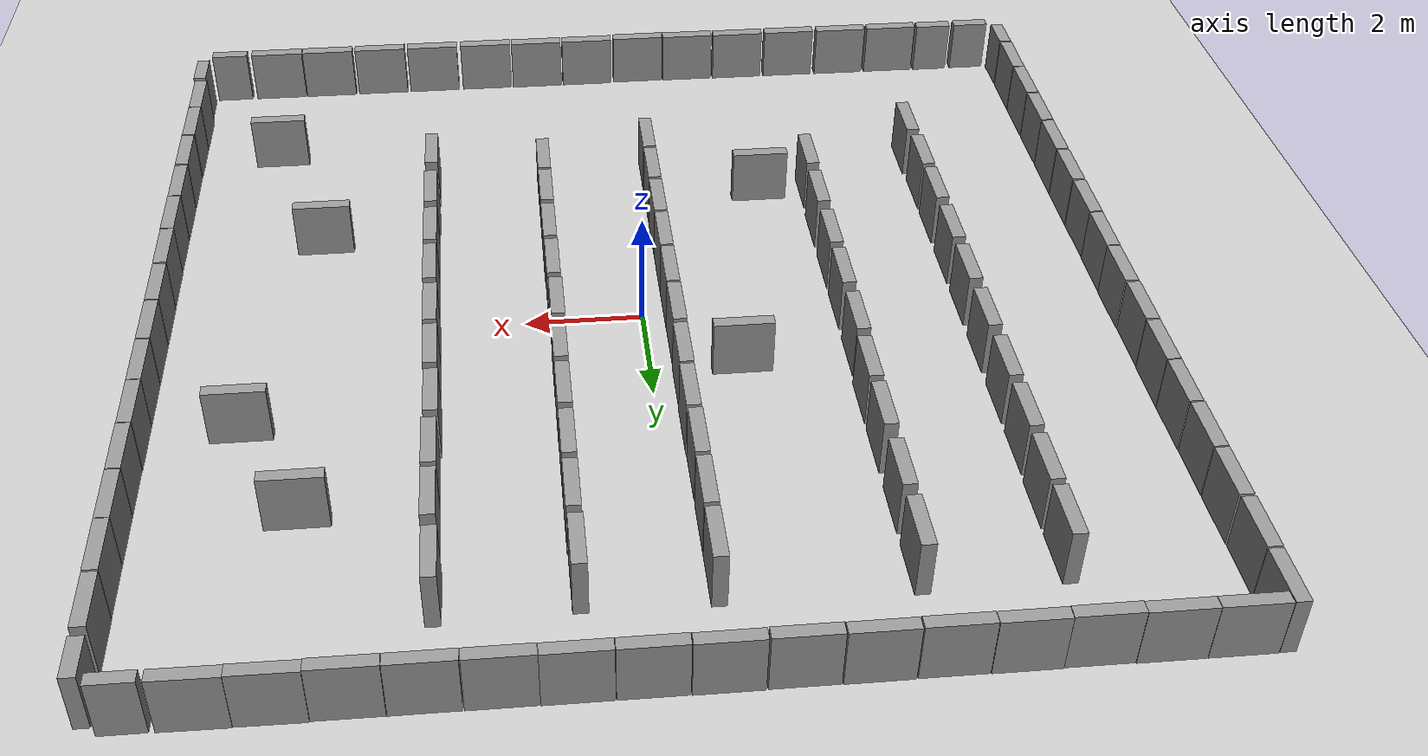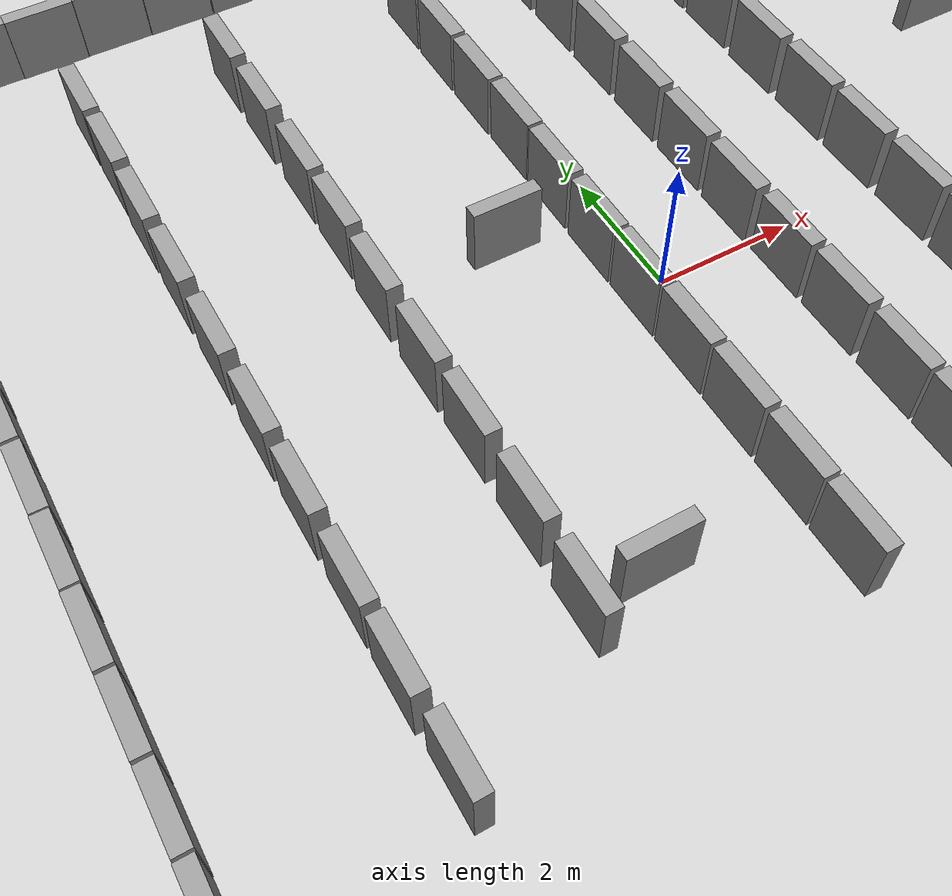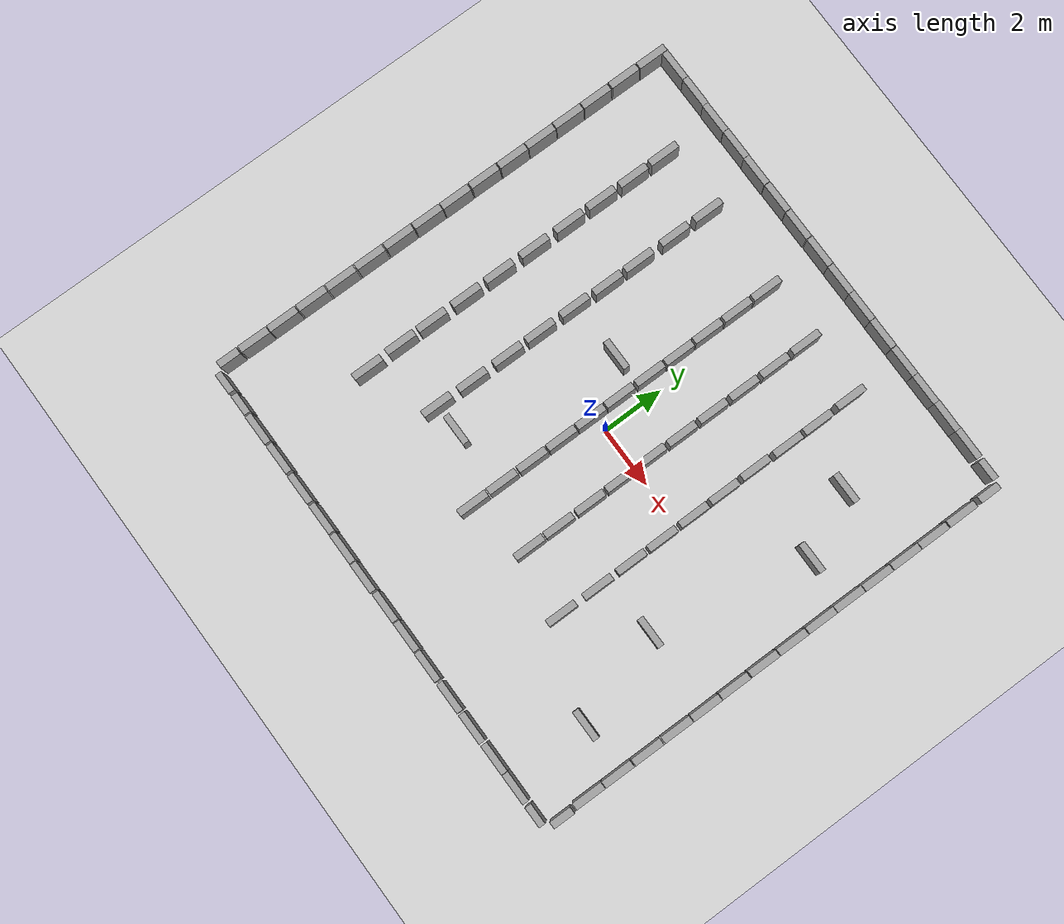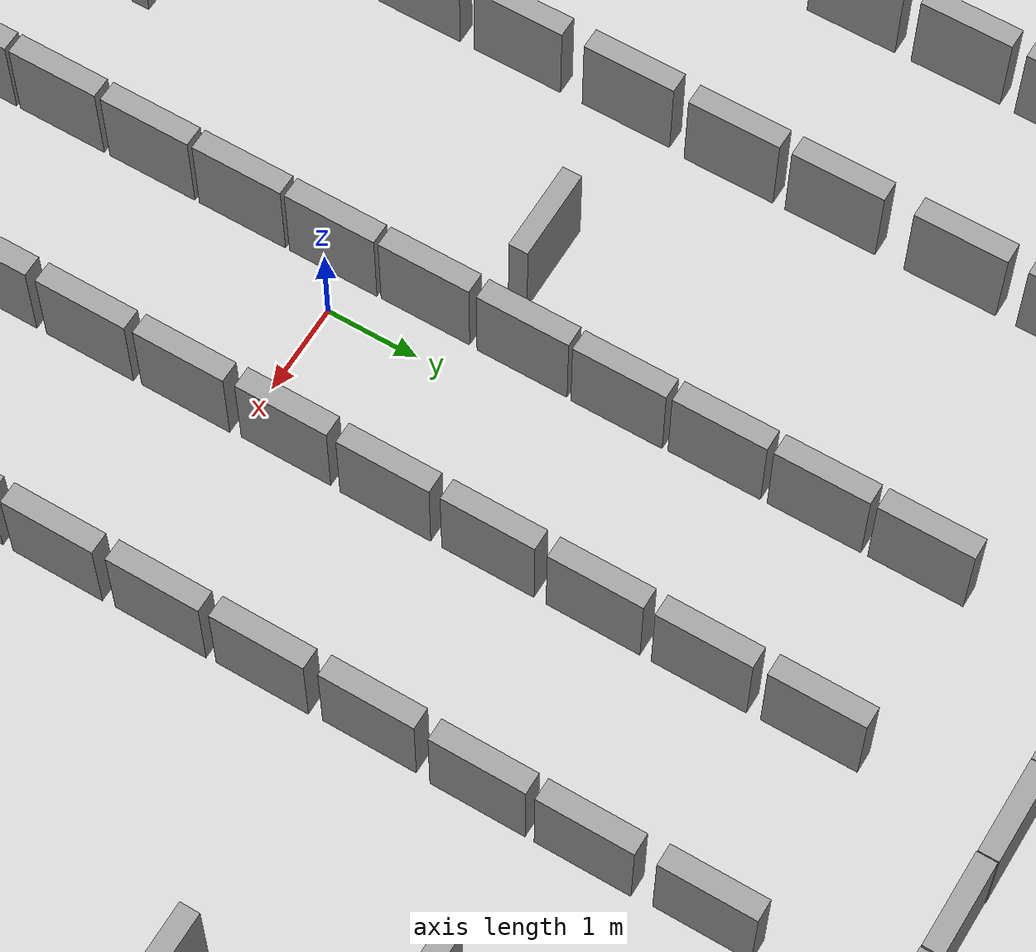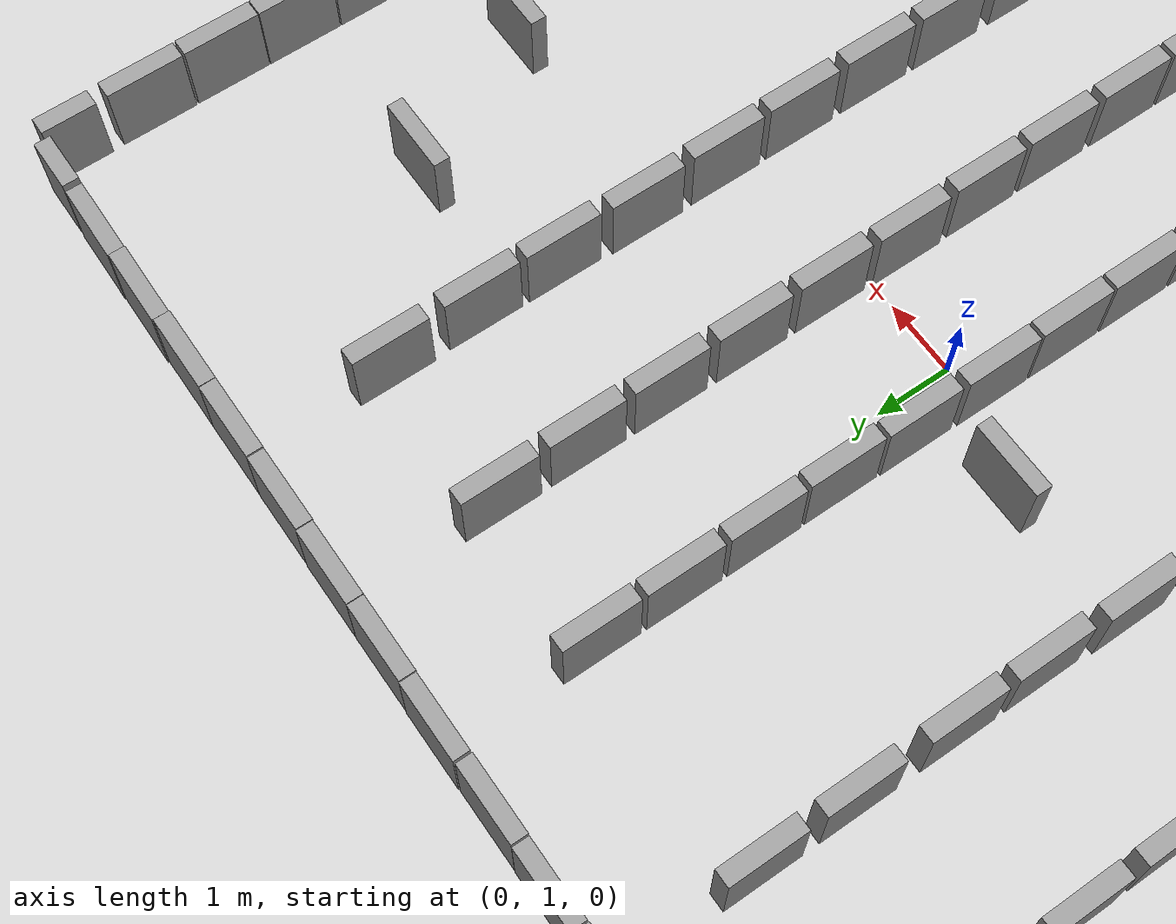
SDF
<sdf version="1.6">
 <world name="default">
  <light name="sun" type="directional">
   <pose>0 0 10 0 -0 0</pose>
   <diffuse>0.8 0.8 0.8 1</diffuse>
   <specular>0.1 0.1 0.1 1</specular>
   <attenuation>
    <range>1000</range>
    <constant>0.9</constant>
    <linear>0.01</linear>
    <quadratic>0.001</quadratic>
   </attenuation>
   <direction>-0.5 0.5 -1</direction>
  </light>
  <model name="ground_plane">
   <static>1</static>
   <static>1</static>
   <link name="link">
    <collision name="collision">
     <geometry><plane><normal>0 0 1</normal><size>100 100</size></plane></geometry>
     <surface><friction><ode><mu>100</mu><mu2>50</mu2></ode></friction></surface>
    </collision>
    <visual name="visual">
     <cast_shadows>0</cast_shadows>
     <geometry><plane><normal>0 0 1</normal><size>100 100</size></plane></geometry>
     <material>
      <script><uri>file://media/materials/scripts/gazebo.material</uri><name>Gazebo/Grey</name></script>
     </material>
    </visual>
   </link>
  </model>
  <gravity>0 0 -9.8</gravity>
  <magnetic_field>6e-06 2.3e-05 -4.2e-05</magnetic_field>
  <atmosphere type="adiabatic"/>
  <physics name="default_physics" default="0" type="ode">
   <max_step_size>0.001</max_step_size>
   <real_time_factor>1</real_time_factor>
   <real_time_update_rate>1000</real_time_update_rate>
  </physics>
  <scene><ambient>0.4 0.4 0.4 1</ambient><background>0.7 0.7 0.7 1</background><shadows>1</shadows></scene>
  <spherical_coordinates>
   <surface_model>EARTH_WGS84</surface_model>
   <latitude_deg>0</latitude_deg>
   <longitude_deg>0</longitude_deg>
   <elevation>0</elevation>
   <heading_deg>0</heading_deg>
  </spherical_coordinates>
  <audio><device>default</device></audio>
  <model name="unit_box_clone">
   <pose>-7.49846 8.11965 0.500001 0 -2e-06 6.5e-05</pose>
   <link name="link">
    <inertial>
     <mass>1</mass>
     <inertia>
      <ixx>0.166667</ixx>
      <ixy>0</ixy>
      <ixz>0</ixz>
      <iyy>0.166667</iyy>
      <iyz>0</iyz>
      <izz>0.166667</izz>
     </inertia>
    </inertial>
    <collision name="collision"><geometry><box><size>1 0.210541 1</size></box></geometry></collision>
    <visual name="visual">
     <geometry><box><size>1 0.210541 1</size></box></geometry>
     <material>
      <script><name>Gazebo/Grey</name><uri>file://media/materials/scripts/gazebo.material</uri></script>
     </material>
    </visual>
   </link>
  </model>
  <model name="unit_box_clone_0">
   <pose>-6.49283 8.11979 0.499997 1e-06 6e-06 -8.5e-05</pose>
   <link name="link">
    <inertial>
     <mass>1</mass>
     <inertia>
      <ixx>0.166667</ixx>
      <ixy>0</ixy>
      <ixz>0</ixz>
      <iyy>0.166667</iyy>
      <iyz>0</iyz>
      <izz>0.166667</izz>
     </inertia>
    </inertial>
    <collision name="collision"><geometry><box><size>1 0.210541 1</size></box></geometry></collision>
    <visual name="visual">
     <geometry><box><size>1 0.210541 1</size></box></geometry>
     <material>
      <script><name>Gazebo/Grey</name><uri>file://media/materials/scripts/gazebo.material</uri></script>
     </material>
    </visual>
   </link>
  </model>
  <model name="unit_box_clone_1">
   <pose>-5.49281 8.10829 0.500001 -0 2e-06 -0.000116</pose>
   <link name="link">
    <inertial>
     <mass>1</mass>
     <inertia>
      <ixx>0.166667</ixx>
      <ixy>0</ixy>
      <ixz>0</ixz>
      <iyy>0.166667</iyy>
      <iyz>0</iyz>
      <izz>0.166667</izz>
     </inertia>
    </inertial>
    <collision name="collision"><geometry><box><size>1 0.210541 1</size></box></geometry></collision>
    <visual name="visual">
     <geometry><box><size>1 0.210541 1</size></box></geometry>
     <material>
      <script><name>Gazebo/Grey</name><uri>file://media/materials/scripts/gazebo.material</uri></script>
     </material>
    </visual>
   </link>
  </model>
  <model name="unit_box_clone_2">
   <pose>-4.48767 8.11835 0.500001 0 -2e-06 6.5e-05</pose>
   <link name="link">
    <inertial>
     <mass>1</mass>
     <inertia>
      <ixx>0.166667</ixx>
      <ixy>0</ixy>
      <ixz>0</ixz>
      <iyy>0.166667</iyy>
      <iyz>0</iyz>
      <izz>0.166667</izz>
     </inertia>
    </inertial>
    <collision name="collision"><geometry><box><size>1 0.210541 1</size></box></geometry></collision>
    <visual name="visual">
     <geometry><box><size>1 0.210541 1</size></box></geometry>
     <material>
      <script><name>Gazebo/Grey</name><uri>file://media/materials/scripts/gazebo.material</uri></script>
     </material>
    </visual>
   </link>
  </model>
  <model name="unit_box_clone_3">
   <pose>-3.48208 8.11168 0.500001 0 -2e-06 6.5e-05</pose>
   <link name="link">
    <inertial>
     <mass>1</mass>
     <inertia>
      <ixx>0.166667</ixx>
      <ixy>0</ixy>
      <ixz>0</ixz>
      <iyy>0.166667</iyy>
      <iyz>0</iyz>
      <izz>0.166667</izz>
     </inertia>
    </inertial>
    <collision name="collision"><geometry><box><size>1 0.210541 1</size></box></geometry></collision>
    <visual name="visual">
     <geometry><box><size>1 0.210541 1</size></box></geometry>
     <material>
      <script><name>Gazebo/Grey</name><uri>file://media/materials/scripts/gazebo.material</uri></script>
     </material>
    </visual>
   </link>
  </model>
  <model name="unit_box_clone_4">
   <pose>-2.46317 8.11834 0.500001 0 -2e-06 6.5e-05</pose>
   <link name="link">
    <inertial>
     <mass>1</mass>
     <inertia>
      <ixx>0.166667</ixx>
      <ixy>0</ixy>
      <ixz>0</ixz>
      <iyy>0.166667</iyy>
      <iyz>0</iyz>
      <izz>0.166667</izz>
     </inertia>
    </inertial>
    <collision name="collision"><geometry><box><size>1 0.210541 1</size></box></geometry></collision>
    <visual name="visual">
     <geometry><box><size>1 0.210541 1</size></box></geometry>
     <material>
      <script><name>Gazebo/Grey</name><uri>file://media/materials/scripts/gazebo.material</uri></script>
     </material>
    </visual>
   </link>
  </model>
  <model name="unit_box_clone_5">
   <pose>-1.44426 8.11168 0.500001 0 -2e-06 6.5e-05</pose>
   <link name="link">
    <inertial>
     <mass>1</mass>
     <inertia>
      <ixx>0.166667</ixx>
      <ixy>0</ixy>
      <ixz>0</ixz>
      <iyy>0.166667</iyy>
      <iyz>0</iyz>
      <izz>0.166667</izz>
     </inertia>
    </inertial>
    <collision name="collision"><geometry><box><size>1 0.210541 1</size></box></geometry></collision>
    <visual name="visual">
     <geometry><box><size>1 0.210541 1</size></box></geometry>
     <material>
      <script><name>Gazebo/Grey</name><uri>file://media/materials/scripts/gazebo.material</uri></script>
     </material>
    </visual>
   </link>
  </model>
  <model name="unit_box_clone_6">
   <pose>-0.418694 8.11833 0.500001 0 -2e-06 6.5e-05</pose>
   <link name="link">
    <inertial>
     <mass>1</mass>
     <inertia>
      <ixx>0.166667</ixx>
      <ixy>0</ixy>
      <ixz>0</ixz>
      <iyy>0.166667</iyy>
      <iyz>0</iyz>
      <izz>0.166667</izz>
     </inertia>
    </inertial>
    <collision name="collision"><geometry><box><size>1 0.210541 1</size></box></geometry></collision>
    <visual name="visual">
     <geometry><box><size>1 0.210541 1</size></box></geometry>
     <material>
      <script><name>Gazebo/Grey</name><uri>file://media/materials/scripts/gazebo.material</uri></script>
     </material>
    </visual>
   </link>
  </model>
  <model name="unit_box_clone_7">
   <pose>0.592825 8.1112 0.500001 0 -2e-06 6.5e-05</pose>
   <link name="link">
    <inertial>
     <mass>1</mass>
     <inertia>
      <ixx>0.166667</ixx>
      <ixy>0</ixy>
      <ixz>0</ixz>
      <iyy>0.166667</iyy>
      <iyz>0</iyz>
      <izz>0.166667</izz>
     </inertia>
    </inertial>
    <collision name="collision"><geometry><box><size>1 0.210541 1</size></box></geometry></collision>
    <visual name="visual">
     <geometry><box><size>1 0.210541 1</size></box></geometry>
     <material>
      <script><name>Gazebo/Grey</name><uri>file://media/materials/scripts/gazebo.material</uri></script>
     </material>
    </visual>
   </link>
  </model>
  <model name="unit_box_clone_8">
   <pose>1.60042 8.10971 0.500001 0 -2e-06 6.5e-05</pose>
   <link name="link">
    <inertial>
     <mass>1</mass>
     <inertia>
      <ixx>0.166667</ixx>
      <ixy>0</ixy>
      <ixz>0</ixz>
      <iyy>0.166667</iyy>
      <iyz>0</iyz>
      <izz>0.166667</izz>
     </inertia>
    </inertial>
    <collision name="collision"><geometry><box><size>1 0.210541 1</size></box></geometry></collision>
    <visual name="visual">
     <geometry><box><size>1 0.210541 1</size></box></geometry>
     <material>
      <script><name>Gazebo/Grey</name><uri>file://media/materials/scripts/gazebo.material</uri></script>
     </material>
    </visual>
   </link>
  </model>
  <model name="unit_box_clone_9">
   <pose>2.60986 8.10252 0.500001 0 -2e-06 6.5e-05</pose>
   <link name="link">
    <inertial>
     <mass>1</mass>
     <inertia>
      <ixx>0.166667</ixx>
      <ixy>0</ixy>
      <ixz>0</ixz>
      <iyy>0.166667</iyy>
      <iyz>0</iyz>
      <izz>0.166667</izz>
     </inertia>
    </inertial>
    <collision name="collision"><geometry><box><size>1 0.210541 1</size></box></geometry></collision>
    <visual name="visual">
     <geometry><box><size>1 0.210541 1</size></box></geometry>
     <material>
      <script><name>Gazebo/Grey</name><uri>file://media/materials/scripts/gazebo.material</uri></script>
     </material>
    </visual>
   </link>
  </model>
  <model name="unit_box_clone_10">
   <pose>3.62648 8.09893 0.500001 0 -2e-06 6.5e-05</pose>
   <link name="link">
    <inertial>
     <mass>1</mass>
     <inertia>
      <ixx>0.166667</ixx>
      <ixy>0</ixy>
      <ixz>0</ixz>
      <iyy>0.166667</iyy>
      <iyz>0</iyz>
      <izz>0.166667</izz>
     </inertia>
    </inertial>
    <collision name="collision"><geometry><box><size>1 0.210541 1</size></box></geometry></collision>
    <visual name="visual">
     <geometry><box><size>1 0.210541 1</size></box></geometry>
     <material>
      <script><name>Gazebo/Grey</name><uri>file://media/materials/scripts/gazebo.material</uri></script>
     </material>
    </visual>
   </link>
  </model>
  <model name="unit_box_clone_11">
   <pose>4.63313 8.09552 0.49995 -0 -1e-06 -0.003223</pose>
   <link name="link">
    <inertial>
     <mass>1</mass>
     <inertia>
      <ixx>0.166667</ixx>
      <ixy>0</ixy>
      <ixz>0</ixz>
      <iyy>0.166667</iyy>
      <iyz>0</iyz>
      <izz>0.166667</izz>
     </inertia>
    </inertial>
    <collision name="collision"><geometry><box><size>1 0.210541 1</size></box></geometry></collision>
    <visual name="visual">
     <geometry><box><size>1 0.210541 1</size></box></geometry>
     <material>
      <script><name>Gazebo/Grey</name><uri>file://media/materials/scripts/gazebo.material</uri></script>
     </material>
    </visual>
   </link>
  </model>
  <model name="unit_box_clone_12">
   <pose>5.63393 8.10254 0.499997 -1e-06 -6e-06 -0.010652</pose>
   <link name="link">
    <inertial>
     <mass>1</mass>
     <inertia>
      <ixx>0.166667</ixx>
      <ixy>0</ixy>
      <ixz>0</ixz>
      <iyy>0.166667</iyy>
      <iyz>0</iyz>
      <izz>0.166667</izz>
     </inertia>
    </inertial>
    <collision name="collision"><geometry><box><size>1 0.210541 1</size></box></geometry></collision>
    <visual name="visual">
     <geometry><box><size>1 0.210541 1</size></box></geometry>
     <material>
      <script><name>Gazebo/Grey</name><uri>file://media/materials/scripts/gazebo.material</uri></script>
     </material>
    </visual>
   </link>
  </model>
  <model name="unit_box_clone_13">
   <pose>6.63405 8.10023 0.49999 1e-06 0 -0.011395</pose>
   <link name="link">
    <inertial>
     <mass>1</mass>
     <inertia>
      <ixx>0.166667</ixx>
      <ixy>0</ixy>
      <ixz>0</ixz>
      <iyy>0.166667</iyy>
      <iyz>0</iyz>
      <izz>0.166667</izz>
     </inertia>
    </inertial>
    <collision name="collision"><geometry><box><size>1 0.210541 1</size></box></geometry></collision>
    <visual name="visual">
     <geometry><box><size>1 0.210541 1</size></box></geometry>
     <material>
      <script><name>Gazebo/Grey</name><uri>file://media/materials/scripts/gazebo.material</uri></script>
     </material>
    </visual>
   </link>
  </model>
  <model name="unit_box_0_clone_0">
   <pose>8.11279 6.68232 0.5 0 -0 7.5e-05</pose>
   <link name="link">
    <inertial>
     <mass>1</mass>
     <inertia>
      <ixx>0.166667</ixx>
      <ixy>0</ixy>
      <ixz>0</ixz>
      <iyy>0.166667</iyy>
      <iyz>0</iyz>
      <izz>0.166667</izz>
     </inertia>
    </inertial>
    <collision name="collision"><geometry><box><size>0.230819 1 1</size></box></geometry></collision>
    <visual name="visual">
     <geometry><box><size>0.230819 1 1</size></box></geometry>
     <material>
      <script><name>Gazebo/Grey</name><uri>file://media/materials/scripts/gazebo.material</uri></script>
     </material>
    </visual>
   </link>
  </model>
  <model name="unit_box_0_clone_1">
   <pose>8.11915 5.6517 0.5 0 -0 7.5e-05</pose>
   <link name="link">
    <inertial>
     <mass>1</mass>
     <inertia>
      <ixx>0.166667</ixx>
      <ixy>0</ixy>
      <ixz>0</ixz>
      <iyy>0.166667</iyy>
      <iyz>0</iyz>
      <izz>0.166667</izz>
     </inertia>
    </inertial>
    <collision name="collision"><geometry><box><size>0.230819 1 1</size></box></geometry></collision>
    <visual name="visual">
     <geometry><box><size>0.230819 1 1</size></box></geometry>
     <material>
      <script><name>Gazebo/Grey</name><uri>file://media/materials/scripts/gazebo.material</uri></script>
     </material>
    </visual>
   </link>
  </model>
  <model name="unit_box_0_clone_2">
   <pose>8.11914 4.64017 0.5 0 -0 7.5e-05</pose>
   <link name="link">
    <inertial>
     <mass>1</mass>
     <inertia>
      <ixx>0.166667</ixx>
      <ixy>0</ixy>
      <ixz>0</ixz>
      <iyy>0.166667</iyy>
      <iyz>0</iyz>
      <izz>0.166667</izz>
     </inertia>
    </inertial>
    <collision name="collision"><geometry><box><size>0.230819 1 1</size></box></geometry></collision>
    <visual name="visual">
     <geometry><box><size>0.230819 1 1</size></box></geometry>
     <material>
      <script><name>Gazebo/Grey</name><uri>file://media/materials/scripts/gazebo.material</uri></script>
     </material>
    </visual>
   </link>
  </model>
  <model name="unit_box_0_clone_3">
   <pose>8.11914 3.62227 0.5 0 -0 7.5e-05</pose>
   <link name="link">
    <inertial>
     <mass>1</mass>
     <inertia>
      <ixx>0.166667</ixx>
      <ixy>0</ixy>
      <ixz>0</ixz>
      <iyy>0.166667</iyy>
      <iyz>0</iyz>
      <izz>0.166667</izz>
     </inertia>
    </inertial>
    <collision name="collision"><geometry><box><size>0.230819 1 1</size></box></geometry></collision>
    <visual name="visual">
     <geometry><box><size>0.230819 1 1</size></box></geometry>
     <material>
      <script><name>Gazebo/Grey</name><uri>file://media/materials/scripts/gazebo.material</uri></script>
     </material>
    </visual>
   </link>
  </model>
  <model name="unit_box_0_clone_4">
   <pose>8.11278 2.61074 0.5 0 -0 7.5e-05</pose>
   <link name="link">
    <inertial>
     <mass>1</mass>
     <inertia>
      <ixx>0.166667</ixx>
      <ixy>0</ixy>
      <ixz>0</ixz>
      <iyy>0.166667</iyy>
      <iyz>0</iyz>
      <izz>0.166667</izz>
     </inertia>
    </inertial>
    <collision name="collision"><geometry><box><size>0.230819 1 1</size></box></geometry></collision>
    <visual name="visual">
     <geometry><box><size>0.230819 1 1</size></box></geometry>
     <material>
      <script><name>Gazebo/Grey</name><uri>file://media/materials/scripts/gazebo.material</uri></script>
     </material>
    </visual>
   </link>
  </model>
  <model name="unit_box_0_clone_5">
   <pose>8.11277 1.5992 0.5 0 -0 7.5e-05</pose>
   <link name="link">
    <inertial>
     <mass>1</mass>
     <inertia>
      <ixx>0.166667</ixx>
      <ixy>0</ixy>
      <ixz>0</ixz>
      <iyy>0.166667</iyy>
      <iyz>0</iyz>
      <izz>0.166667</izz>
     </inertia>
    </inertial>
    <collision name="collision"><geometry><box><size>0.230819 1 1</size></box></geometry></collision>
    <visual name="visual">
     <geometry><box><size>0.230819 1 1</size></box></geometry>
     <material>
      <script><name>Gazebo/Grey</name><uri>file://media/materials/scripts/gazebo.material</uri></script>
     </material>
    </visual>
   </link>
  </model>
  <model name="unit_box_0_clone_6">
   <pose>8.11277 0.574942 0.5 0 -0 7.5e-05</pose>
   <link name="link">
    <inertial>
     <mass>1</mass>
     <inertia>
      <ixx>0.166667</ixx>
      <ixy>0</ixy>
      <ixz>0</ixz>
      <iyy>0.166667</iyy>
      <iyz>0</iyz>
      <izz>0.166667</izz>
     </inertia>
    </inertial>
    <collision name="collision"><geometry><box><size>0.230819 1 1</size></box></geometry></collision>
    <visual name="visual">
     <geometry><box><size>0.230819 1 1</size></box></geometry>
     <material>
      <script><name>Gazebo/Grey</name><uri>file://media/materials/scripts/gazebo.material</uri></script>
     </material>
    </visual>
   </link>
  </model>
  <model name="unit_box_0_clone_7">
   <pose>8.11276 -0.449316 0.5 0 -0 7.5e-05</pose>
   <link name="link">
    <inertial>
     <mass>1</mass>
     <inertia>
      <ixx>0.166667</ixx>
      <ixy>0</ixy>
      <ixz>0</ixz>
      <iyy>0.166667</iyy>
      <iyz>0</iyz>
      <izz>0.166667</izz>
     </inertia>
    </inertial>
    <collision name="collision"><geometry><box><size>0.230819 1 1</size></box></geometry></collision>
    <visual name="visual">
     <geometry><box><size>0.230819 1 1</size></box></geometry>
     <material>
      <script><name>Gazebo/Grey</name><uri>file://media/materials/scripts/gazebo.material</uri></script>
     </material>
    </visual>
   </link>
  </model>
  <model name="unit_box_0_clone_8">
   <pose>8.11912 -1.4863 0.5 0 -0 7.5e-05</pose>
   <link name="link">
    <inertial>
     <mass>1</mass>
     <inertia>
      <ixx>0.166667</ixx>
      <ixy>0</ixy>
      <ixz>0</ixz>
      <iyy>0.166667</iyy>
      <iyz>0</iyz>
      <izz>0.166667</izz>
     </inertia>
    </inertial>
    <collision name="collision"><geometry><box><size>0.230819 1 1</size></box></geometry></collision>
    <visual name="visual">
     <geometry><box><size>0.230819 1 1</size></box></geometry>
     <material>
      <script><name>Gazebo/Grey</name><uri>file://media/materials/scripts/gazebo.material</uri></script>
     </material>
    </visual>
   </link>
  </model>
  <model name="unit_box_0_clone_9">
   <pose>8.12548 -2.5042 0.5 0 -0 7.5e-05</pose>
   <link name="link">
    <inertial>
     <mass>1</mass>
     <inertia>
      <ixx>0.166667</ixx>
      <ixy>0</ixy>
      <ixz>0</ixz>
      <iyy>0.166667</iyy>
      <iyz>0</iyz>
      <izz>0.166667</izz>
     </inertia>
    </inertial>
    <collision name="collision"><geometry><box><size>0.230819 1 1</size></box></geometry></collision>
    <visual name="visual">
     <geometry><box><size>0.230819 1 1</size></box></geometry>
     <material>
      <script><name>Gazebo/Grey</name><uri>file://media/materials/scripts/gazebo.material</uri></script>
     </material>
    </visual>
   </link>
  </model>
  <model name="unit_box_0_clone_10">
   <pose>8.12331 -3.52222 0.5 0 -0 7.5e-05</pose>
   <link name="link">
    <inertial>
     <mass>1</mass>
     <inertia>
      <ixx>0.166667</ixx>
      <ixy>0</ixy>
      <ixz>0</ixz>
      <iyy>0.166667</iyy>
      <iyz>0</iyz>
      <izz>0.166667</izz>
     </inertia>
    </inertial>
    <collision name="collision"><geometry><box><size>0.230819 1 1</size></box></geometry></collision>
    <visual name="visual">
     <geometry><box><size>0.230819 1 1</size></box></geometry>
     <material>
      <script><name>Gazebo/Grey</name><uri>file://media/materials/scripts/gazebo.material</uri></script>
     </material>
    </visual>
   </link>
  </model>
  <model name="unit_box_0_clone_11">
   <pose>8.1233 -4.56315 0.5 0 -0 7.5e-05</pose>
   <link name="link">
    <inertial>
     <mass>1</mass>
     <inertia>
      <ixx>0.166667</ixx>
      <ixy>0</ixy>
      <ixz>0</ixz>
      <iyy>0.166667</iyy>
      <iyz>0</iyz>
      <izz>0.166667</izz>
     </inertia>
    </inertial>
    <collision name="collision"><geometry><box><size>0.230819 1 1</size></box></geometry></collision>
    <visual name="visual">
     <geometry><box><size>0.230819 1 1</size></box></geometry>
     <material>
      <script><name>Gazebo/Grey</name><uri>file://media/materials/scripts/gazebo.material</uri></script>
     </material>
    </visual>
   </link>
  </model>
  <model name="unit_box_0_clone_12">
   <pose>8.11815 -5.59377 0.5 0 -0 7.5e-05</pose>
   <link name="link">
    <inertial>
     <mass>1</mass>
     <inertia>
      <ixx>0.166667</ixx>
      <ixy>0</ixy>
      <ixz>0</ixz>
      <iyy>0.166667</iyy>
      <iyz>0</iyz>
      <izz>0.166667</izz>
     </inertia>
    </inertial>
    <collision name="collision"><geometry><box><size>0.230819 1 1</size></box></geometry></collision>
    <visual name="visual">
     <geometry><box><size>0.230819 1 1</size></box></geometry>
     <material>
      <script><name>Gazebo/Grey</name><uri>file://media/materials/scripts/gazebo.material</uri></script>
     </material>
    </visual>
   </link>
  </model>
  <model name="unit_box_0_clone_13">
   <pose>8.11333 -6.60775 0.499998 3e-06 1e-06 -0.00551</pose>
   <link name="link">
    <inertial>
     <mass>1</mass>
     <inertia>
      <ixx>0.166667</ixx>
      <ixy>0</ixy>
      <ixz>0</ixz>
      <iyy>0.166667</iyy>
      <iyz>0</iyz>
      <izz>0.166667</izz>
     </inertia>
    </inertial>
    <collision name="collision"><geometry><box><size>0.230819 1 1</size></box></geometry></collision>
    <visual name="visual">
     <geometry><box><size>0.230819 1 1</size></box></geometry>
     <material>
      <script><name>Gazebo/Grey</name><uri>file://media/materials/scripts/gazebo.material</uri></script>
     </material>
    </visual>
   </link>
  </model>
  <model name="unit_box_clone_15_clone_0">
   <pose>6.71206 -8.13139 0.500001 0 -2e-06 6.5e-05</pose>
   <link name="link">
    <inertial>
     <mass>1</mass>
     <inertia>
      <ixx>0.166667</ixx>
      <ixy>0</ixy>
      <ixz>0</ixz>
      <iyy>0.166667</iyy>
      <iyz>0</iyz>
      <izz>0.166667</izz>
     </inertia>
    </inertial>
    <collision name="collision"><geometry><box><size>1 0.210541 1</size></box></geometry></collision>
    <visual name="visual">
     <geometry><box><size>1 0.210541 1</size></box></geometry>
     <material>
      <script><name>Gazebo/Grey</name><uri>file://media/materials/scripts/gazebo.material</uri></script>
     </material>
    </visual>
   </link>
  </model>
  <model name="unit_box_clone_15_clone_1">
   <pose>5.69714 -8.13138 0.500001 0 -2e-06 6.5e-05</pose>
   <link name="link">
    <inertial>
     <mass>1</mass>
     <inertia>
      <ixx>0.166667</ixx>
      <ixy>0</ixy>
      <ixz>0</ixz>
      <iyy>0.166667</iyy>
      <iyz>0</iyz>
      <izz>0.166667</izz>
     </inertia>
    </inertial>
    <collision name="collision"><geometry><box><size>1 0.210541 1</size></box></geometry></collision>
    <visual name="visual">
     <geometry><box><size>1 0.210541 1</size></box></geometry>
     <material>
      <script><name>Gazebo/Grey</name><uri>file://media/materials/scripts/gazebo.material</uri></script>
     </material>
    </visual>
   </link>
  </model>
  <model name="unit_box_clone_15_clone_2">
   <pose>4.6388 -8.13756 0.500001 0 -2e-06 6.5e-05</pose>
   <link name="link">
    <inertial>
     <mass>1</mass>
     <inertia>
      <ixx>0.166667</ixx>
      <ixy>0</ixy>
      <ixz>0</ixz>
      <iyy>0.166667</iyy>
      <iyz>0</iyz>
      <izz>0.166667</izz>
     </inertia>
    </inertial>
    <collision name="collision"><geometry><box><size>1 0.210541 1</size></box></geometry></collision>
    <visual name="visual">
     <geometry><box><size>1 0.210541 1</size></box></geometry>
     <material>
      <script><name>Gazebo/Grey</name><uri>file://media/materials/scripts/gazebo.material</uri></script>
     </material>
    </visual>
   </link>
  </model>
  <model name="unit_box_clone_15_clone_3">
   <pose>3.57974 -8.13756 0.500001 0 -2e-06 6.5e-05</pose>
   <link name="link">
    <inertial>
     <mass>1</mass>
     <inertia>
      <ixx>0.166667</ixx>
      <ixy>0</ixy>
      <ixz>0</ixz>
      <iyy>0.166667</iyy>
      <iyz>0</iyz>
      <izz>0.166667</izz>
     </inertia>
    </inertial>
    <collision name="collision"><geometry><box><size>1 0.210541 1</size></box></geometry></collision>
    <visual name="visual">
     <geometry><box><size>1 0.210541 1</size></box></geometry>
     <material>
      <script><name>Gazebo/Grey</name><uri>file://media/materials/scripts/gazebo.material</uri></script>
     </material>
    </visual>
   </link>
  </model>
  <model name="unit_box_clone_15_clone_4">
   <pose>2.49814 -8.13755 0.500001 0 -2e-06 6.5e-05</pose>
   <link name="link">
    <inertial>
     <mass>1</mass>
     <inertia>
      <ixx>0.166667</ixx>
      <ixy>0</ixy>
      <ixz>0</ixz>
      <iyy>0.166667</iyy>
      <iyz>0</iyz>
      <izz>0.166667</izz>
     </inertia>
    </inertial>
    <collision name="collision"><geometry><box><size>1 0.210541 1</size></box></geometry></collision>
    <visual name="visual">
     <geometry><box><size>1 0.210541 1</size></box></geometry>
     <material>
      <script><name>Gazebo/Grey</name><uri>file://media/materials/scripts/gazebo.material</uri></script>
     </material>
    </visual>
   </link>
  </model>
  <model name="unit_box_clone_15_clone_5">
   <pose>1.46161 -8.12628 0.500001 0 -2e-06 6.5e-05</pose>
   <link name="link">
    <inertial>
     <mass>1</mass>
     <inertia>
      <ixx>0.166667</ixx>
      <ixy>0</ixy>
      <ixz>0</ixz>
      <iyy>0.166667</iyy>
      <iyz>0</iyz>
      <izz>0.166667</izz>
     </inertia>
    </inertial>
    <collision name="collision"><geometry><box><size>1 0.210541 1</size></box></geometry></collision>
    <visual name="visual">
     <geometry><box><size>1 0.210541 1</size></box></geometry>
     <material>
      <script><name>Gazebo/Grey</name><uri>file://media/materials/scripts/gazebo.material</uri></script>
     </material>
    </visual>
   </link>
  </model>
  <model name="unit_box_clone_15_clone_6">
   <pose>0.425078 -8.12627 0.500001 0 -2e-06 6.5e-05</pose>
   <link name="link">
    <inertial>
     <mass>1</mass>
     <inertia>
      <ixx>0.166667</ixx>
      <ixy>0</ixy>
      <ixz>0</ixz>
      <iyy>0.166667</iyy>
      <iyz>0</iyz>
      <izz>0.166667</izz>
     </inertia>
    </inertial>
    <collision name="collision"><geometry><box><size>1 0.210541 1</size></box></geometry></collision>
    <visual name="visual">
     <geometry><box><size>1 0.210541 1</size></box></geometry>
     <material>
      <script><name>Gazebo/Grey</name><uri>file://media/materials/scripts/gazebo.material</uri></script>
     </material>
    </visual>
   </link>
  </model>
  <model name="unit_box_clone_15_clone_7">
   <pose>-0.633984 -8.14882 0.500001 0 -2e-06 6.5e-05</pose>
   <link name="link">
    <inertial>
     <mass>1</mass>
     <inertia>
      <ixx>0.166667</ixx>
      <ixy>0</ixy>
      <ixz>0</ixz>
      <iyy>0.166667</iyy>
      <iyz>0</iyz>
      <izz>0.166667</izz>
     </inertia>
    </inertial>
    <collision name="collision"><geometry><box><size>1 0.210541 1</size></box></geometry></collision>
    <visual name="visual">
     <geometry><box><size>1 0.210541 1</size></box></geometry>
     <material>
      <script><name>Gazebo/Grey</name><uri>file://media/materials/scripts/gazebo.material</uri></script>
     </material>
    </visual>
   </link>
  </model>
  <model name="unit_box_clone_15_clone_8">
   <pose>-1.65924 -8.13754 0.500001 0 -2e-06 6.5e-05</pose>
   <link name="link">
    <inertial>
     <mass>1</mass>
     <inertia>
      <ixx>0.166667</ixx>
      <ixy>0</ixy>
      <ixz>0</ixz>
      <iyy>0.166667</iyy>
      <iyz>0</iyz>
      <izz>0.166667</izz>
     </inertia>
    </inertial>
    <collision name="collision"><geometry><box><size>1 0.210541 1</size></box></geometry></collision>
    <visual name="visual">
     <geometry><box><size>1 0.210541 1</size></box></geometry>
     <material>
      <script><name>Gazebo/Grey</name><uri>file://media/materials/scripts/gazebo.material</uri></script>
     </material>
    </visual>
   </link>
  </model>
  <model name="unit_box_clone_15_clone_9">
   <pose>-2.70704 -8.12629 0.500001 0 -2e-06 6.5e-05</pose>
   <link name="link">
    <inertial>
     <mass>1</mass>
     <inertia>
      <ixx>0.166667</ixx>
      <ixy>0</ixy>
      <ixz>0</ixz>
      <iyy>0.166667</iyy>
      <iyz>0</iyz>
      <izz>0.166667</izz>
     </inertia>
    </inertial>
    <collision name="collision"><geometry><box><size>1 0.210541 1</size></box></geometry></collision>
    <visual name="visual">
     <geometry><box><size>1 0.210541 1</size></box></geometry>
     <material>
      <script><name>Gazebo/Grey</name><uri>file://media/materials/scripts/gazebo.material</uri></script>
     </material>
    </visual>
   </link>
  </model>
  <model name="unit_box_clone_15_clone_10">
   <pose>-3.77737 -8.12628 0.500001 0 -2e-06 6.5e-05</pose>
   <link name="link">
    <inertial>
     <mass>1</mass>
     <inertia>
      <ixx>0.166667</ixx>
      <ixy>0</ixy>
      <ixz>0</ixz>
      <iyy>0.166667</iyy>
      <iyz>0</iyz>
      <izz>0.166667</izz>
     </inertia>
    </inertial>
    <collision name="collision"><geometry><box><size>1 0.210541 1</size></box></geometry></collision>
    <visual name="visual">
     <geometry><box><size>1 0.210541 1</size></box></geometry>
     <material>
      <script><name>Gazebo/Grey</name><uri>file://media/materials/scripts/gazebo.material</uri></script>
     </material>
    </visual>
   </link>
  </model>
  <model name="unit_box_clone_15_clone_11">
   <pose>-4.85897 -8.11502 0.500001 0 -2e-06 6.5e-05</pose>
   <link name="link">
    <inertial>
     <mass>1</mass>
     <inertia>
      <ixx>0.166667</ixx>
      <ixy>0</ixy>
      <ixz>0</ixz>
      <iyy>0.166667</iyy>
      <iyz>0</iyz>
      <izz>0.166667</izz>
     </inertia>
    </inertial>
    <collision name="collision"><geometry><box><size>1 0.210541 1</size></box></geometry></collision>
    <visual name="visual">
     <geometry><box><size>1 0.210541 1</size></box></geometry>
     <material>
      <script><name>Gazebo/Grey</name><uri>file://media/materials/scripts/gazebo.material</uri></script>
     </material>
    </visual>
   </link>
  </model>
  <model name="unit_box_clone_15_clone_12">
   <pose>-5.91803 -8.11501 0.500001 0 -2e-06 6.5e-05</pose>
   <link name="link">
    <inertial>
     <mass>1</mass>
     <inertia>
      <ixx>0.166667</ixx>
      <ixy>0</ixy>
      <ixz>0</ixz>
      <iyy>0.166667</iyy>
      <iyz>0</iyz>
      <izz>0.166667</izz>
     </inertia>
    </inertial>
    <collision name="collision"><geometry><box><size>1 0.210541 1</size></box></geometry></collision>
    <visual name="visual">
     <geometry><box><size>1 0.210541 1</size></box></geometry>
     <material>
      <script><name>Gazebo/Grey</name><uri>file://media/materials/scripts/gazebo.material</uri></script>
     </material>
    </visual>
   </link>
  </model>
  <model name="unit_box_0_clone_4_clone">
   <pose>-8.12647 7.71769 0.5 0 -0 7.5e-05</pose>
   <link name="link">
    <inertial>
     <mass>1</mass>
     <inertia>
      <ixx>0.166667</ixx>
      <ixy>0</ixy>
      <ixz>0</ixz>
      <iyy>0.166667</iyy>
      <iyz>0</iyz>
      <izz>0.166667</izz>
     </inertia>
    </inertial>
    <collision name="collision"><geometry><box><size>0.230819 1 1</size></box></geometry></collision>
    <visual name="visual">
     <geometry><box><size>0.230819 1 1</size></box></geometry>
     <material>
      <script><name>Gazebo/Grey</name><uri>file://media/materials/scripts/gazebo.material</uri></script>
     </material>
    </visual>
   </link>
  </model>
  <model name="unit_box_0_clone_4_clone_0">
   <pose>-8.13281 6.68715 0.5 0 -0 7.5e-05</pose>
   <link name="link">
    <inertial>
     <mass>1</mass>
     <inertia>
      <ixx>0.166667</ixx>
      <ixy>0</ixy>
      <ixz>0</ixz>
      <iyy>0.166667</iyy>
      <iyz>0</iyz>
      <izz>0.166667</izz>
     </inertia>
    </inertial>
    <collision name="collision"><geometry><box><size>0.230819 1 1</size></box></geometry></collision>
    <visual name="visual">
     <geometry><box><size>0.230819 1 1</size></box></geometry>
     <material>
      <script><name>Gazebo/Grey</name><uri>file://media/materials/scripts/gazebo.material</uri></script>
     </material>
    </visual>
   </link>
  </model>
  <model name="unit_box_0_clone_4_clone_1">
   <pose>-8.12606 5.64723 0.5 0 -0 7.5e-05</pose>
   <link name="link">
    <inertial>
     <mass>1</mass>
     <inertia>
      <ixx>0.166667</ixx>
      <ixy>0</ixy>
      <ixz>0</ixz>
      <iyy>0.166667</iyy>
      <iyz>0</iyz>
      <izz>0.166667</izz>
     </inertia>
    </inertial>
    <collision name="collision"><geometry><box><size>0.230819 1 1</size></box></geometry></collision>
    <visual name="visual">
     <geometry><box><size>0.230819 1 1</size></box></geometry>
     <material>
      <script><name>Gazebo/Grey</name><uri>file://media/materials/scripts/gazebo.material</uri></script>
     </material>
    </visual>
   </link>
  </model>
  <model name="unit_box_0_clone_4_clone_2">
   <pose>-8.12607 4.62081 0.5 0 -0 7.5e-05</pose>
   <link name="link">
    <inertial>
     <mass>1</mass>
     <inertia>
      <ixx>0.166667</ixx>
      <ixy>0</ixy>
      <ixz>0</ixz>
      <iyy>0.166667</iyy>
      <iyz>0</iyz>
      <izz>0.166667</izz>
     </inertia>
    </inertial>
    <collision name="collision"><geometry><box><size>0.230819 1 1</size></box></geometry></collision>
    <visual name="visual">
     <geometry><box><size>0.230819 1 1</size></box></geometry>
     <material>
      <script><name>Gazebo/Grey</name><uri>file://media/materials/scripts/gazebo.material</uri></script>
     </material>
    </visual>
   </link>
  </model>
  <model name="unit_box_0_clone_4_clone_3">
   <pose>-8.11932 3.59439 0.5 0 -0 7.5e-05</pose>
   <link name="link">
    <inertial>
     <mass>1</mass>
     <inertia>
      <ixx>0.166667</ixx>
      <ixy>0</ixy>
      <ixz>0</ixz>
      <iyy>0.166667</iyy>
      <iyz>0</iyz>
      <izz>0.166667</izz>
     </inertia>
    </inertial>
    <collision name="collision"><geometry><box><size>0.230819 1 1</size></box></geometry></collision>
    <visual name="visual">
     <geometry><box><size>0.230819 1 1</size></box></geometry>
     <material>
      <script><name>Gazebo/Grey</name><uri>file://media/materials/scripts/gazebo.material</uri></script>
     </material>
    </visual>
   </link>
  </model>
  <model name="unit_box_0_clone_4_clone_4">
   <pose>-8.11932 2.57473 0.5 0 -0 7.5e-05</pose>
   <link name="link">
    <inertial>
     <mass>1</mass>
     <inertia>
      <ixx>0.166667</ixx>
      <ixy>0</ixy>
      <ixz>0</ixz>
      <iyy>0.166667</iyy>
      <iyz>0</iyz>
      <izz>0.166667</izz>
     </inertia>
    </inertial>
    <collision name="collision"><geometry><box><size>0.230819 1 1</size></box></geometry></collision>
    <visual name="visual">
     <geometry><box><size>0.230819 1 1</size></box></geometry>
     <material>
      <script><name>Gazebo/Grey</name><uri>file://media/materials/scripts/gazebo.material</uri></script>
     </material>
    </visual>
   </link>
  </model>
  <model name="unit_box_0_clone_4_clone_5">
   <pose>-8.12608 1.54156 0.5 0 -0 7.5e-05</pose>
   <link name="link">
    <inertial>
     <mass>1</mass>
     <inertia>
      <ixx>0.166667</ixx>
      <ixy>0</ixy>
      <ixz>0</ixz>
      <iyy>0.166667</iyy>
      <iyz>0</iyz>
      <izz>0.166667</izz>
     </inertia>
    </inertial>
    <collision name="collision"><geometry><box><size>0.230819 1 1</size></box></geometry></collision>
    <visual name="visual">
     <geometry><box><size>0.230819 1 1</size></box></geometry>
     <material>
      <script><name>Gazebo/Grey</name><uri>file://media/materials/scripts/gazebo.material</uri></script>
     </material>
    </visual>
   </link>
  </model>
  <model name="unit_box_0_clone_4_clone_6">
   <pose>-8.11933 0.501634 0.5 0 -0 7.5e-05</pose>
   <link name="link">
    <inertial>
     <mass>1</mass>
     <inertia>
      <ixx>0.166667</ixx>
      <ixy>0</ixy>
      <ixz>0</ixz>
      <iyy>0.166667</iyy>
      <iyz>0</iyz>
      <izz>0.166667</izz>
     </inertia>
    </inertial>
    <collision name="collision"><geometry><box><size>0.230819 1 1</size></box></geometry></collision>
    <visual name="visual">
     <geometry><box><size>0.230819 1 1</size></box></geometry>
     <material>
      <script><name>Gazebo/Grey</name><uri>file://media/materials/scripts/gazebo.material</uri></script>
     </material>
    </visual>
   </link>
  </model>
  <model name="unit_box_0_clone_4_clone_7">
   <pose>-8.12609 -0.51803 0.5 0 -0 7.5e-05</pose>
   <link name="link">
    <inertial>
     <mass>1</mass>
     <inertia>
      <ixx>0.166667</ixx>
      <ixy>0</ixy>
      <ixz>0</ixz>
      <iyy>0.166667</iyy>
      <iyz>0</iyz>
      <izz>0.166667</izz>
     </inertia>
    </inertial>
    <collision name="collision"><geometry><box><size>0.230819 1 1</size></box></geometry></collision>
    <visual name="visual">
     <geometry><box><size>0.230819 1 1</size></box></geometry>
     <material>
      <script><name>Gazebo/Grey</name><uri>file://media/materials/scripts/gazebo.material</uri></script>
     </material>
    </visual>
   </link>
  </model>
  <model name="unit_box_0_clone_4_clone_8">
   <pose>-8.13284 -1.54445 0.5 0 -0 7.5e-05</pose>
   <link name="link">
    <inertial>
     <mass>1</mass>
     <inertia>
      <ixx>0.166667</ixx>
      <ixy>0</ixy>
      <ixz>0</ixz>
      <iyy>0.166667</iyy>
      <iyz>0</iyz>
      <izz>0.166667</izz>
     </inertia>
    </inertial>
    <collision name="collision"><geometry><box><size>0.230819 1 1</size></box></geometry></collision>
    <visual name="visual">
     <geometry><box><size>0.230819 1 1</size></box></geometry>
     <material>
      <script><name>Gazebo/Grey</name><uri>file://media/materials/scripts/gazebo.material</uri></script>
     </material>
    </visual>
   </link>
  </model>
  <model name="unit_box_0_clone_4_clone_9">
   <pose>-8.13285 -2.58437 0.5 0 -0 7.5e-05</pose>
   <link name="link">
    <inertial>
     <mass>1</mass>
     <inertia>
      <ixx>0.166667</ixx>
      <ixy>0</ixy>
      <ixz>0</ixz>
      <iyy>0.166667</iyy>
      <iyz>0</iyz>
      <izz>0.166667</izz>
     </inertia>
    </inertial>
    <collision name="collision"><geometry><box><size>0.230819 1 1</size></box></geometry></collision>
    <visual name="visual">
     <geometry><box><size>0.230819 1 1</size></box></geometry>
     <material>
      <script><name>Gazebo/Grey</name><uri>file://media/materials/scripts/gazebo.material</uri></script>
     </material>
    </visual>
   </link>
  </model>
  <model name="unit_box_0_clone_4_clone_10">
   <pose>-8.13285 -3.62429 0.5 0 -0 7.5e-05</pose>
   <link name="link">
    <inertial>
     <mass>1</mass>
     <inertia>
      <ixx>0.166667</ixx>
      <ixy>0</ixy>
      <ixz>0</ixz>
      <iyy>0.166667</iyy>
      <iyz>0</iyz>
      <izz>0.166667</izz>
     </inertia>
    </inertial>
    <collision name="collision"><geometry><box><size>0.230819 1 1</size></box></geometry></collision>
    <visual name="visual">
     <geometry><box><size>0.230819 1 1</size></box></geometry>
     <material>
      <script><name>Gazebo/Grey</name><uri>file://media/materials/scripts/gazebo.material</uri></script>
     </material>
    </visual>
   </link>
  </model>
  <model name="unit_box_0_clone_4_clone_11">
   <pose>-8.1396 -4.65746 0.5 0 -0 7.5e-05</pose>
   <link name="link">
    <inertial>
     <mass>1</mass>
     <inertia>
      <ixx>0.166667</ixx>
      <ixy>0</ixy>
      <ixz>0</ixz>
      <iyy>0.166667</iyy>
      <iyz>0</iyz>
      <izz>0.166667</izz>
     </inertia>
    </inertial>
    <collision name="collision"><geometry><box><size>0.230819 1 1</size></box></geometry></collision>
    <visual name="visual">
     <geometry><box><size>0.230819 1 1</size></box></geometry>
     <material>
      <script><name>Gazebo/Grey</name><uri>file://media/materials/scripts/gazebo.material</uri></script>
     </material>
    </visual>
   </link>
  </model>
  <model name="unit_box_0_clone_4_clone_12">
   <pose>-8.1396 -5.69063 0.5 0 -0 7.5e-05</pose>
   <link name="link">
    <inertial>
     <mass>1</mass>
     <inertia>
      <ixx>0.166667</ixx>
      <ixy>0</ixy>
      <ixz>0</ixz>
      <iyy>0.166667</iyy>
      <iyz>0</iyz>
      <izz>0.166667</izz>
     </inertia>
    </inertial>
    <collision name="collision"><geometry><box><size>0.230819 1 1</size></box></geometry></collision>
    <visual name="visual">
     <geometry><box><size>0.230819 1 1</size></box></geometry>
     <material>
      <script><name>Gazebo/Grey</name><uri>file://media/materials/scripts/gazebo.material</uri></script>
     </material>
    </visual>
   </link>
  </model>
  <model name="unit_box_0_clone_4_clone_13">
   <pose>-8.14113 -6.70872 0.5 0 -0 -0.009849</pose>
   <link name="link">
    <inertial>
     <mass>1</mass>
     <inertia>
      <ixx>0.166667</ixx>
      <ixy>0</ixy>
      <ixz>0</ixz>
      <iyy>0.166667</iyy>
      <iyz>0</iyz>
      <izz>0.166667</izz>
     </inertia>
    </inertial>
    <collision name="collision"><geometry><box><size>0.230819 1 1</size></box></geometry></collision>
    <visual name="visual">
     <geometry><box><size>0.230819 1 1</size></box></geometry>
     <material>
      <script><name>Gazebo/Grey</name><uri>file://media/materials/scripts/gazebo.material</uri></script>
     </material>
    </visual>
   </link>
  </model>
  <model name="unit_box_0_clone_4_clone_1_clone">
   <pose>-5.52752 6.20788 0.5 0 -0 7.5e-05</pose>
   <link name="link">
    <inertial>
     <mass>1</mass>
     <inertia>
      <ixx>0.166667</ixx>
      <ixy>0</ixy>
      <ixz>0</ixz>
      <iyy>0.166667</iyy>
      <iyz>0</iyz>
      <izz>0.166667</izz>
     </inertia>
    </inertial>
    <collision name="collision"><geometry><box><size>0.230819 1 1</size></box></geometry></collision>
    <visual name="visual">
     <geometry><box><size>0.230819 1 1</size></box></geometry>
     <material>
      <script><name>Gazebo/Grey</name><uri>file://media/materials/scripts/gazebo.material</uri></script>
     </material>
    </visual>
   </link>
  </model>
  <model name="unit_box_0_clone_4_clone_1_clone_0">
   <pose>-5.52753 5.0919 0.5 0 -0 7.5e-05</pose>
   <link name="link">
    <inertial>
     <mass>1</mass>
     <inertia>
      <ixx>0.166667</ixx>
      <ixy>0</ixy>
      <ixz>0</ixz>
      <iyy>0.166667</iyy>
      <iyz>0</iyz>
      <izz>0.166667</izz>
     </inertia>
    </inertial>
    <collision name="collision"><geometry><box><size>0.230819 1 1</size></box></geometry></collision>
    <visual name="visual">
     <geometry><box><size>0.230819 1 1</size></box></geometry>
     <material>
      <script><name>Gazebo/Grey</name><uri>file://media/materials/scripts/gazebo.material</uri></script>
     </material>
    </visual>
   </link>
  </model>
  <model name="unit_box_0_clone_4_clone_1_clone_1">
   <pose>-5.54419 3.92594 0.5 0 -0 7.5e-05</pose>
   <link name="link">
    <inertial>
     <mass>1</mass>
     <inertia>
      <ixx>0.166667</ixx>
      <ixy>0</ixy>
      <ixz>0</ixz>
      <iyy>0.166667</iyy>
      <iyz>0</iyz>
      <izz>0.166667</izz>
     </inertia>
    </inertial>
    <collision name="collision"><geometry><box><size>0.230819 1 1</size></box></geometry></collision>
    <visual name="visual">
     <geometry><box><size>0.230819 1 1</size></box></geometry>
     <material>
      <script><name>Gazebo/Grey</name><uri>file://media/materials/scripts/gazebo.material</uri></script>
     </material>
    </visual>
   </link>
  </model>
  <model name="unit_box_0_clone_4_clone_1_clone_2">
   <pose>-5.5442 2.74333 0.5 0 -0 7.5e-05</pose>
   <link name="link">
    <inertial>
     <mass>1</mass>
     <inertia>
      <ixx>0.166667</ixx>
      <ixy>0</ixy>
      <ixz>0</ixz>
      <iyy>0.166667</iyy>
      <iyz>0</iyz>
      <izz>0.166667</izz>
     </inertia>
    </inertial>
    <collision name="collision"><geometry><box><size>0.230819 1 1</size></box></geometry></collision>
    <visual name="visual">
     <geometry><box><size>0.230819 1 1</size></box></geometry>
     <material>
      <script><name>Gazebo/Grey</name><uri>file://media/materials/scripts/gazebo.material</uri></script>
     </material>
    </visual>
   </link>
  </model>
  <model name="unit_box_0_clone_4_clone_1_clone_3">
   <pose>-5.5442 1.47744 0.5 0 -0 7.5e-05</pose>
   <link name="link">
    <inertial>
     <mass>1</mass>
     <inertia>
      <ixx>0.166667</ixx>
      <ixy>0</ixy>
      <ixz>0</ixz>
      <iyy>0.166667</iyy>
      <iyz>0</iyz>
      <izz>0.166667</izz>
     </inertia>
    </inertial>
    <collision name="collision"><geometry><box><size>0.230819 1 1</size></box></geometry></collision>
    <visual name="visual">
     <geometry><box><size>0.230819 1 1</size></box></geometry>
     <material>
      <script><name>Gazebo/Grey</name><uri>file://media/materials/scripts/gazebo.material</uri></script>
     </material>
    </visual>
   </link>
  </model>
  <model name="unit_box_0_clone_4_clone_1_clone_4">
   <pose>-5.54421 0.211547 0.5 0 -0 7.5e-05</pose>
   <link name="link">
    <inertial>
     <mass>1</mass>
     <inertia>
      <ixx>0.166667</ixx>
      <ixy>0</ixy>
      <ixz>0</ixz>
      <iyy>0.166667</iyy>
      <iyz>0</iyz>
      <izz>0.166667</izz>
     </inertia>
    </inertial>
    <collision name="collision"><geometry><box><size>0.230819 1 1</size></box></geometry></collision>
    <visual name="visual">
     <geometry><box><size>0.230819 1 1</size></box></geometry>
     <material>
      <script><name>Gazebo/Grey</name><uri>file://media/materials/scripts/gazebo.material</uri></script>
     </material>
    </visual>
   </link>
  </model>
  <model name="unit_box_0_clone_4_clone_1_clone_5">
   <pose>-5.54422 -0.98772 0.5 0 -0 7.5e-05</pose>
   <link name="link">
    <inertial>
     <mass>1</mass>
     <inertia>
      <ixx>0.166667</ixx>
      <ixy>0</ixy>
      <ixz>0</ixz>
      <iyy>0.166667</iyy>
      <iyz>0</iyz>
      <izz>0.166667</izz>
     </inertia>
    </inertial>
    <collision name="collision"><geometry><box><size>0.230819 1 1</size></box></geometry></collision>
    <visual name="visual">
     <geometry><box><size>0.230819 1 1</size></box></geometry>
     <material>
      <script><name>Gazebo/Grey</name><uri>file://media/materials/scripts/gazebo.material</uri></script>
     </material>
    </visual>
   </link>
  </model>
  <model name="unit_box_0_clone_4_clone_1_clone_6">
   <pose>-5.54422 -2.2203 0.5 0 -0 7.5e-05</pose>
   <link name="link">
    <inertial>
     <mass>1</mass>
     <inertia>
      <ixx>0.166667</ixx>
      <ixy>0</ixy>
      <ixz>0</ixz>
      <iyy>0.166667</iyy>
      <iyz>0</iyz>
      <izz>0.166667</izz>
     </inertia>
    </inertial>
    <collision name="collision"><geometry><box><size>0.230819 1 1</size></box></geometry></collision>
    <visual name="visual">
     <geometry><box><size>0.230819 1 1</size></box></geometry>
     <material>
      <script><name>Gazebo/Grey</name><uri>file://media/materials/scripts/gazebo.material</uri></script>
     </material>
    </visual>
   </link>
  </model>
  <model name="unit_box_0_clone_4_clone_1_clone_7">
   <pose>-5.54423 -3.33629 0.5 0 -0 7.5e-05</pose>
   <link name="link">
    <inertial>
     <mass>1</mass>
     <inertia>
      <ixx>0.166667</ixx>
      <ixy>0</ixy>
      <ixz>0</ixz>
      <iyy>0.166667</iyy>
      <iyz>0</iyz>
      <izz>0.166667</izz>
     </inertia>
    </inertial>
    <collision name="collision"><geometry><box><size>0.230819 1 1</size></box></geometry></collision>
    <visual name="visual">
     <geometry><box><size>0.230819 1 1</size></box></geometry>
     <material>
      <script><name>Gazebo/Grey</name><uri>file://media/materials/scripts/gazebo.material</uri></script>
     </material>
    </visual>
   </link>
  </model>
  <model name="unit_box_0_clone_4_clone_1_clone_8">
   <pose>-5.51092 -4.53555 0.5 0 -0 7.5e-05</pose>
   <link name="link">
    <inertial>
     <mass>1</mass>
     <inertia>
      <ixx>0.166667</ixx>
      <ixy>0</ixy>
      <ixz>0</ixz>
      <iyy>0.166667</iyy>
      <iyz>0</iyz>
      <izz>0.166667</izz>
     </inertia>
    </inertial>
    <collision name="collision"><geometry><box><size>0.230819 1 1</size></box></geometry></collision>
    <visual name="visual">
     <geometry><box><size>0.230819 1 1</size></box></geometry>
     <material>
      <script><name>Gazebo/Grey</name><uri>file://media/materials/scripts/gazebo.material</uri></script>
     </material>
    </visual>
   </link>
  </model>
  <model name="unit_box_0_clone_4_clone_1_clone_10">
   <pose>-3.37884 6.22453 0.5 0 -0 7.5e-05</pose>
   <link name="link">
    <inertial>
     <mass>1</mass>
     <inertia>
      <ixx>0.166667</ixx>
      <ixy>0</ixy>
      <ixz>0</ixz>
      <iyy>0.166667</iyy>
      <iyz>0</iyz>
      <izz>0.166667</izz>
     </inertia>
    </inertial>
    <collision name="collision"><geometry><box><size>0.230819 1 1</size></box></geometry></collision>
    <visual name="visual">
     <geometry><box><size>0.230819 1 1</size></box></geometry>
     <material>
      <script><name>Gazebo/Grey</name><uri>file://media/materials/scripts/gazebo.material</uri></script>
     </material>
    </visual>
   </link>
  </model>
  <model name="unit_box_0_clone_4_clone_1_clone_11">
   <pose>-3.37884 5.0086 0.5 0 -0 7.5e-05</pose>
   <link name="link">
    <inertial>
     <mass>1</mass>
     <inertia>
      <ixx>0.166667</ixx>
      <ixy>0</ixy>
      <ixz>0</ixz>
      <iyy>0.166667</iyy>
      <iyz>0</iyz>
      <izz>0.166667</izz>
     </inertia>
    </inertial>
    <collision name="collision"><geometry><box><size>0.230819 1 1</size></box></geometry></collision>
    <visual name="visual">
     <geometry><box><size>0.230819 1 1</size></box></geometry>
     <material>
      <script><name>Gazebo/Grey</name><uri>file://media/materials/scripts/gazebo.material</uri></script>
     </material>
    </visual>
   </link>
  </model>
  <model name="unit_box_0_clone_4_clone_1_clone_12">
   <pose>-3.37885 3.69274 0.5 0 -0 7.5e-05</pose>
   <link name="link">
    <inertial>
     <mass>1</mass>
     <inertia>
      <ixx>0.166667</ixx>
      <ixy>0</ixy>
      <ixz>0</ixz>
      <iyy>0.166667</iyy>
      <iyz>0</iyz>
      <izz>0.166667</izz>
     </inertia>
    </inertial>
    <collision name="collision"><geometry><box><size>0.230819 1 1</size></box></geometry></collision>
    <visual name="visual">
     <geometry><box><size>0.230819 1 1</size></box></geometry>
     <material>
      <script><name>Gazebo/Grey</name><uri>file://media/materials/scripts/gazebo.material</uri></script>
     </material>
    </visual>
   </link>
  </model>
  <model name="unit_box_0_clone_4_clone_1_clone_13">
   <pose>-3.37886 2.5601 0.5 0 -0 7.5e-05</pose>
   <link name="link">
    <inertial>
     <mass>1</mass>
     <inertia>
      <ixx>0.166667</ixx>
      <ixy>0</ixy>
      <ixz>0</ixz>
      <iyy>0.166667</iyy>
      <iyz>0</iyz>
      <izz>0.166667</izz>
     </inertia>
    </inertial>
    <collision name="collision"><geometry><box><size>0.230819 1 1</size></box></geometry></collision>
    <visual name="visual">
     <geometry><box><size>0.230819 1 1</size></box></geometry>
     <material>
      <script><name>Gazebo/Grey</name><uri>file://media/materials/scripts/gazebo.material</uri></script>
     </material>
    </visual>
   </link>
  </model>
  <model name="unit_box_0_clone_4_clone_1_clone_14">
   <pose>-3.41218 1.37749 0.5 0 -0 7.5e-05</pose>
   <link name="link">
    <inertial>
     <mass>1</mass>
     <inertia>
      <ixx>0.166667</ixx>
      <ixy>0</ixy>
      <ixz>0</ixz>
      <iyy>0.166667</iyy>
      <iyz>0</iyz>
      <izz>0.166667</izz>
     </inertia>
    </inertial>
    <collision name="collision"><geometry><box><size>0.230819 1 1</size></box></geometry></collision>
    <visual name="visual">
     <geometry><box><size>0.230819 1 1</size></box></geometry>
     <material>
      <script><name>Gazebo/Grey</name><uri>file://media/materials/scripts/gazebo.material</uri></script>
     </material>
    </visual>
   </link>
  </model>
  <model name="unit_box_0_clone_4_clone_1_clone_15">
   <pose>-3.41218 0.128253 0.5 0 -0 7.5e-05</pose>
   <link name="link">
    <inertial>
     <mass>1</mass>
     <inertia>
      <ixx>0.166667</ixx>
      <ixy>0</ixy>
      <ixz>0</ixz>
      <iyy>0.166667</iyy>
      <iyz>0</iyz>
      <izz>0.166667</izz>
     </inertia>
    </inertial>
    <collision name="collision"><geometry><box><size>0.230819 1 1</size></box></geometry></collision>
    <visual name="visual">
     <geometry><box><size>0.230819 1 1</size></box></geometry>
     <material>
      <script><name>Gazebo/Grey</name><uri>file://media/materials/scripts/gazebo.material</uri></script>
     </material>
    </visual>
   </link>
  </model>
  <model name="unit_box_0_clone_4_clone_1_clone_16">
   <pose>-3.41219 -1.0377 0.5 0 -0 7.5e-05</pose>
   <link name="link">
    <inertial>
     <mass>1</mass>
     <inertia>
      <ixx>0.166667</ixx>
      <ixy>0</ixy>
      <ixz>0</ixz>
      <iyy>0.166667</iyy>
      <iyz>0</iyz>
      <izz>0.166667</izz>
     </inertia>
    </inertial>
    <collision name="collision"><geometry><box><size>0.230819 1 1</size></box></geometry></collision>
    <visual name="visual">
     <geometry><box><size>0.230819 1 1</size></box></geometry>
     <material>
      <script><name>Gazebo/Grey</name><uri>file://media/materials/scripts/gazebo.material</uri></script>
     </material>
    </visual>
   </link>
  </model>
  <model name="unit_box_0_clone_4_clone_1_clone_17">
   <pose>-3.41219 -2.3036 0.5 0 -0 7.5e-05</pose>
   <link name="link">
    <inertial>
     <mass>1</mass>
     <inertia>
      <ixx>0.166667</ixx>
      <ixy>0</ixy>
      <ixz>0</ixz>
      <iyy>0.166667</iyy>
      <iyz>0</iyz>
      <izz>0.166667</izz>
     </inertia>
    </inertial>
    <collision name="collision"><geometry><box><size>0.230819 1 1</size></box></geometry></collision>
    <visual name="visual">
     <geometry><box><size>0.230819 1 1</size></box></geometry>
     <material>
      <script><name>Gazebo/Grey</name><uri>file://media/materials/scripts/gazebo.material</uri></script>
     </material>
    </visual>
   </link>
  </model>
  <model name="unit_box_0_clone_4_clone_1_clone_18">
   <pose>-3.42886 -3.55283 0.5 0 -0 7.5e-05</pose>
   <link name="link">
    <inertial>
     <mass>1</mass>
     <inertia>
      <ixx>0.166667</ixx>
      <ixy>0</ixy>
      <ixz>0</ixz>
      <iyy>0.166667</iyy>
      <iyz>0</iyz>
      <izz>0.166667</izz>
     </inertia>
    </inertial>
    <collision name="collision"><geometry><box><size>0.230819 1 1</size></box></geometry></collision>
    <visual name="visual">
     <geometry><box><size>0.230819 1 1</size></box></geometry>
     <material>
      <script><name>Gazebo/Grey</name><uri>file://media/materials/scripts/gazebo.material</uri></script>
     </material>
    </visual>
   </link>
  </model>
  <model name="unit_box_0_clone_4_clone_1_clone_10_clone">
   <pose>-0.482286 6.18572 0.5 0 -0 7.5e-05</pose>
   <link name="link">
    <inertial>
     <mass>1</mass>
     <inertia>
      <ixx>0.166667</ixx>
      <ixy>0</ixy>
      <ixz>0</ixz>
      <iyy>0.166667</iyy>
      <iyz>0</iyz>
      <izz>0.166667</izz>
     </inertia>
    </inertial>
    <collision name="collision"><geometry><box><size>0.230819 1 1</size></box></geometry></collision>
    <visual name="visual">
     <geometry><box><size>0.230819 1 1</size></box></geometry>
     <material>
      <script><name>Gazebo/Grey</name><uri>file://media/materials/scripts/gazebo.material</uri></script>
     </material>
    </visual>
   </link>
  </model>
  <model name="unit_box_0_clone_4_clone_1_clone_10_clone_0">
   <pose>-0.482292 5.11618 0.5 0 -0 7.5e-05</pose>
   <link name="link">
    <inertial>
     <mass>1</mass>
     <inertia>
      <ixx>0.166667</ixx>
      <ixy>0</ixy>
      <ixz>0</ixz>
      <iyy>0.166667</iyy>
      <iyz>0</iyz>
      <izz>0.166667</izz>
     </inertia>
    </inertial>
    <collision name="collision"><geometry><box><size>0.230819 1 1</size></box></geometry></collision>
    <visual name="visual">
     <geometry><box><size>0.230819 1 1</size></box></geometry>
     <material>
      <script><name>Gazebo/Grey</name><uri>file://media/materials/scripts/gazebo.material</uri></script>
     </material>
    </visual>
   </link>
  </model>
  <model name="unit_box_0_clone_4_clone_1_clone_10_clone_1">
   <pose>-0.482297 4.04665 0.5 0 -0 7.5e-05</pose>
   <link name="link">
    <inertial>
     <mass>1</mass>
     <inertia>
      <ixx>0.166667</ixx>
      <ixy>0</ixy>
      <ixz>0</ixz>
      <iyy>0.166667</iyy>
      <iyz>0</iyz>
      <izz>0.166667</izz>
     </inertia>
    </inertial>
    <collision name="collision"><geometry><box><size>0.230819 1 1</size></box></geometry></collision>
    <visual name="visual">
     <geometry><box><size>0.230819 1 1</size></box></geometry>
     <material>
      <script><name>Gazebo/Grey</name><uri>file://media/materials/scripts/gazebo.material</uri></script>
     </material>
    </visual>
   </link>
  </model>
  <model name="unit_box_0_clone_4_clone_1_clone_10_clone_2">
   <pose>-0.472918 2.98968 0.5 0 -0 7.5e-05</pose>
   <link name="link">
    <inertial>
     <mass>1</mass>
     <inertia>
      <ixx>0.166667</ixx>
      <ixy>0</ixy>
      <ixz>0</ixz>
      <iyy>0.166667</iyy>
      <iyz>0</iyz>
      <izz>0.166667</izz>
     </inertia>
    </inertial>
    <collision name="collision"><geometry><box><size>0.230819 1 1</size></box></geometry></collision>
    <visual name="visual">
     <geometry><box><size>0.230819 1 1</size></box></geometry>
     <material>
      <script><name>Gazebo/Grey</name><uri>file://media/materials/scripts/gazebo.material</uri></script>
     </material>
    </visual>
   </link>
  </model>
  <model name="unit_box_0_clone_4_clone_1_clone_10_clone_3">
   <pose>-0.482806 1.94204 0.5 0 -0 7.5e-05</pose>
   <link name="link">
    <inertial>
     <mass>1</mass>
     <inertia>
      <ixx>0.166667</ixx>
      <ixy>0</ixy>
      <ixz>0</ixz>
      <iyy>0.166667</iyy>
      <iyz>0</iyz>
      <izz>0.166667</izz>
     </inertia>
    </inertial>
    <collision name="collision"><geometry><box><size>0.230819 1 1</size></box></geometry></collision>
    <visual name="visual">
     <geometry><box><size>0.230819 1 1</size></box></geometry>
     <material>
      <script><name>Gazebo/Grey</name><uri>file://media/materials/scripts/gazebo.material</uri></script>
     </material>
    </visual>
   </link>
  </model>
  <model name="unit_box_0_clone_4_clone_1_clone_10_clone_4">
   <pose>-0.492695 0.854868 0.5 0 -0 7.5e-05</pose>
   <link name="link">
    <inertial>
     <mass>1</mass>
     <inertia>
      <ixx>0.166667</ixx>
      <ixy>0</ixy>
      <ixz>0</ixz>
      <iyy>0.166667</iyy>
      <iyz>0</iyz>
      <izz>0.166667</izz>
     </inertia>
    </inertial>
    <collision name="collision"><geometry><box><size>0.230819 1 1</size></box></geometry></collision>
    <visual name="visual">
     <geometry><box><size>0.230819 1 1</size></box></geometry>
     <material>
      <script><name>Gazebo/Grey</name><uri>file://media/materials/scripts/gazebo.material</uri></script>
     </material>
    </visual>
   </link>
  </model>
  <model name="unit_box_0_clone_4_clone_1_clone_10_clone_4_clone">
   <pose>-0.489359 -0.189024 0.5 0 -0 7.5e-05</pose>
   <link name="link">
    <inertial>
     <mass>1</mass>
     <inertia>
      <ixx>0.166667</ixx>
      <ixy>0</ixy>
      <ixz>0</ixz>
      <iyy>0.166667</iyy>
      <iyz>0</iyz>
      <izz>0.166667</izz>
     </inertia>
    </inertial>
    <collision name="collision"><geometry><box><size>0.230819 1 1</size></box></geometry></collision>
    <visual name="visual">
     <geometry><box><size>0.230819 1 1</size></box></geometry>
     <material>
      <script><name>Gazebo/Grey</name><uri>file://media/materials/scripts/gazebo.material</uri></script>
     </material>
    </visual>
   </link>
  </model>
  <model name="unit_box_0_clone_4_clone_1_clone_10_clone_4_clone_0">
   <pose>-0.489365 -1.23375 0.5 0 -0 7.5e-05</pose>
   <link name="link">
    <inertial>
     <mass>1</mass>
     <inertia>
      <ixx>0.166667</ixx>
      <ixy>0</ixy>
      <ixz>0</ixz>
      <iyy>0.166667</iyy>
      <iyz>0</iyz>
      <izz>0.166667</izz>
     </inertia>
    </inertial>
    <collision name="collision"><geometry><box><size>0.230819 1 1</size></box></geometry></collision>
    <visual name="visual">
     <geometry><box><size>0.230819 1 1</size></box></geometry>
     <material>
      <script><name>Gazebo/Grey</name><uri>file://media/materials/scripts/gazebo.material</uri></script>
     </material>
    </visual>
   </link>
  </model>
  <model name="unit_box_0_clone_4_clone_1_clone_10_clone_4_clone_1">
   <pose>-0.489371 -2.28567 0.5 0 -0 7.5e-05</pose>
   <link name="link">
    <inertial>
     <mass>1</mass>
     <inertia>
      <ixx>0.166667</ixx>
      <ixy>0</ixy>
      <ixz>0</ixz>
      <iyy>0.166667</iyy>
      <iyz>0</iyz>
      <izz>0.166667</izz>
     </inertia>
    </inertial>
    <collision name="collision"><geometry><box><size>0.230819 1 1</size></box></geometry></collision>
    <visual name="visual">
     <geometry><box><size>0.230819 1 1</size></box></geometry>
     <material>
      <script><name>Gazebo/Grey</name><uri>file://media/materials/scripts/gazebo.material</uri></script>
     </material>
    </visual>
   </link>
  </model>
  <model name="unit_box_0_clone_4_clone_1_clone_10_clone_4_clone_2">
   <pose>-0.489376 -3.35201 0.5 0 -0 7.5e-05</pose>
   <link name="link">
    <inertial>
     <mass>1</mass>
     <inertia>
      <ixx>0.166667</ixx>
      <ixy>0</ixy>
      <ixz>0</ixz>
      <iyy>0.166667</iyy>
      <iyz>0</iyz>
      <izz>0.166667</izz>
     </inertia>
    </inertial>
    <collision name="collision"><geometry><box><size>0.230819 1 1</size></box></geometry></collision>
    <visual name="visual">
     <geometry><box><size>0.230819 1 1</size></box></geometry>
     <material>
      <script><name>Gazebo/Grey</name><uri>file://media/materials/scripts/gazebo.material</uri></script>
     </material>
    </visual>
   </link>
  </model>
  <model name="unit_box_0_clone_4_clone_1_clone_10_clone_4_clone_3">
   <pose>-0.489382 -4.39673 0.5 0 -0 7.5e-05</pose>
   <link name="link">
    <inertial>
     <mass>1</mass>
     <inertia>
      <ixx>0.166667</ixx>
      <ixy>0</ixy>
      <ixz>0</ixz>
      <iyy>0.166667</iyy>
      <iyz>0</iyz>
      <izz>0.166667</izz>
     </inertia>
    </inertial>
    <collision name="collision"><geometry><box><size>0.230819 1 1</size></box></geometry></collision>
    <visual name="visual">
     <geometry><box><size>0.230819 1 1</size></box></geometry>
     <material>
      <script><name>Gazebo/Grey</name><uri>file://media/materials/scripts/gazebo.material</uri></script>
     </material>
    </visual>
   </link>
  </model>
  <model name="unit_box_0_clone_4_clone_1_clone_10_clone_clone">
   <pose>1.47105 6.14198 0.5 0 -0 7.5e-05</pose>
   <link name="link">
    <inertial>
     <mass>1</mass>
     <inertia>
      <ixx>0.166667</ixx>
      <ixy>0</ixy>
      <ixz>0</ixz>
      <iyy>0.166667</iyy>
      <iyz>0</iyz>
      <izz>0.166667</izz>
     </inertia>
    </inertial>
    <collision name="collision"><geometry><box><size>0.230819 1 1</size></box></geometry></collision>
    <visual name="visual">
     <geometry><box><size>0.230819 1 1</size></box></geometry>
     <material>
      <script><name>Gazebo/Grey</name><uri>file://media/materials/scripts/gazebo.material</uri></script>
     </material>
    </visual>
   </link>
  </model>
  <model name="unit_box_0_clone_4_clone_1_clone_10_clone_clone_0">
   <pose>1.48169 5.00224 0.5 0 -0 7.5e-05</pose>
   <link name="link">
    <inertial>
     <mass>1</mass>
     <inertia>
      <ixx>0.166667</ixx>
      <ixy>0</ixy>
      <ixz>0</ixz>
      <iyy>0.166667</iyy>
      <iyz>0</iyz>
      <izz>0.166667</izz>
     </inertia>
    </inertial>
    <collision name="collision"><geometry><box><size>0.230819 1 1</size></box></geometry></collision>
    <visual name="visual">
     <geometry><box><size>0.230819 1 1</size></box></geometry>
     <material>
      <script><name>Gazebo/Grey</name><uri>file://media/materials/scripts/gazebo.material</uri></script>
     </material>
    </visual>
   </link>
  </model>
  <model name="unit_box_0_clone_4_clone_1_clone_10_clone_clone_1">
   <pose>1.48169 3.8838 0.5 0 -0 7.5e-05</pose>
   <link name="link">
    <inertial>
     <mass>1</mass>
     <inertia>
      <ixx>0.166667</ixx>
      <ixy>0</ixy>
      <ixz>0</ixz>
      <iyy>0.166667</iyy>
      <iyz>0</iyz>
      <izz>0.166667</izz>
     </inertia>
    </inertial>
    <collision name="collision"><geometry><box><size>0.230819 1 1</size></box></geometry></collision>
    <visual name="visual">
     <geometry><box><size>0.230819 1 1</size></box></geometry>
     <material>
      <script><name>Gazebo/Grey</name><uri>file://media/materials/scripts/gazebo.material</uri></script>
     </material>
    </visual>
   </link>
  </model>
  <model name="unit_box_0_clone_4_clone_1_clone_10_clone_clone_2">
   <pose>1.48168 2.75471 0.5 0 -0 7.5e-05</pose>
   <link name="link">
    <inertial>
     <mass>1</mass>
     <inertia>
      <ixx>0.166667</ixx>
      <ixy>0</ixy>
      <ixz>0</ixz>
      <iyy>0.166667</iyy>
      <iyz>0</iyz>
      <izz>0.166667</izz>
     </inertia>
    </inertial>
    <collision name="collision"><geometry><box><size>0.230819 1 1</size></box></geometry></collision>
    <visual name="visual">
     <geometry><box><size>0.230819 1 1</size></box></geometry>
     <material>
      <script><name>Gazebo/Grey</name><uri>file://media/materials/scripts/gazebo.material</uri></script>
     </material>
    </visual>
   </link>
  </model>
  <model name="unit_box_0_clone_4_clone_1_clone_10_clone_clone_3">
   <pose>1.48167 1.63627 0.5 0 -0 7.5e-05</pose>
   <link name="link">
    <inertial>
     <mass>1</mass>
     <inertia>
      <ixx>0.166667</ixx>
      <ixy>0</ixy>
      <ixz>0</ixz>
      <iyy>0.166667</iyy>
      <iyz>0</iyz>
      <izz>0.166667</izz>
     </inertia>
    </inertial>
    <collision name="collision"><geometry><box><size>0.230819 1 1</size></box></geometry></collision>
    <visual name="visual">
     <geometry><box><size>0.230819 1 1</size></box></geometry>
     <material>
      <script><name>Gazebo/Grey</name><uri>file://media/materials/scripts/gazebo.material</uri></script>
     </material>
    </visual>
   </link>
  </model>
  <model name="unit_box_0_clone_4_clone_1_clone_10_clone_clone_4">
   <pose>1.47102 0.528487 0.5 0 -0 7.5e-05</pose>
   <link name="link">
    <inertial>
     <mass>1</mass>
     <inertia>
      <ixx>0.166667</ixx>
      <ixy>0</ixy>
      <ixz>0</ixz>
      <iyy>0.166667</iyy>
      <iyz>0</iyz>
      <izz>0.166667</izz>
     </inertia>
    </inertial>
    <collision name="collision"><geometry><box><size>0.230819 1 1</size></box></geometry></collision>
    <visual name="visual">
     <geometry><box><size>0.230819 1 1</size></box></geometry>
     <material>
      <script><name>Gazebo/Grey</name><uri>file://media/materials/scripts/gazebo.material</uri></script>
     </material>
    </visual>
   </link>
  </model>
  <model name="unit_box_0_clone_4_clone_1_clone_10_clone_clone_5">
   <pose>1.48667 -0.590057 0.5 0 -0 7.5e-05</pose>
   <link name="link">
    <inertial>
     <mass>1</mass>
     <inertia>
      <ixx>0.166667</ixx>
      <ixy>0</ixy>
      <ixz>0</ixz>
      <iyy>0.166667</iyy>
      <iyz>0</iyz>
      <izz>0.166667</izz>
     </inertia>
    </inertial>
    <collision name="collision"><geometry><box><size>0.230819 1 1</size></box></geometry></collision>
    <visual name="visual">
     <geometry><box><size>0.230819 1 1</size></box></geometry>
     <material>
      <script><name>Gazebo/Grey</name><uri>file://media/materials/scripts/gazebo.material</uri></script>
     </material>
    </visual>
   </link>
  </model>
  <model name="unit_box_0_clone_4_clone_1_clone_10_clone_clone_6">
   <pose>1.49529 -1.67718 0.5 0 -0 7.5e-05</pose>
   <link name="link">
    <inertial>
     <mass>1</mass>
     <inertia>
      <ixx>0.166667</ixx>
      <ixy>0</ixy>
      <ixz>0</ixz>
      <iyy>0.166667</iyy>
      <iyz>0</iyz>
      <izz>0.166667</izz>
     </inertia>
    </inertial>
    <collision name="collision"><geometry><box><size>0.230819 1 1</size></box></geometry></collision>
    <visual name="visual">
     <geometry><box><size>0.230819 1 1</size></box></geometry>
     <material>
      <script><name>Gazebo/Grey</name><uri>file://media/materials/scripts/gazebo.material</uri></script>
     </material>
    </visual>
   </link>
  </model>
  <model name="unit_box_0_clone_4_clone_1_clone_10_clone_clone_7">
   <pose>1.49529 -2.79018 0.5 0 -0 7.5e-05</pose>
   <link name="link">
    <inertial>
     <mass>1</mass>
     <inertia>
      <ixx>0.166667</ixx>
      <ixy>0</ixy>
      <ixz>0</ixz>
      <iyy>0.166667</iyy>
      <iyz>0</iyz>
      <izz>0.166667</izz>
     </inertia>
    </inertial>
    <collision name="collision"><geometry><box><size>0.230819 1 1</size></box></geometry></collision>
    <visual name="visual">
     <geometry><box><size>0.230819 1 1</size></box></geometry>
     <material>
      <script><name>Gazebo/Grey</name><uri>file://media/materials/scripts/gazebo.material</uri></script>
     </material>
    </visual>
   </link>
  </model>
  <model name="unit_box_0_clone_4_clone_1_clone_10_clone_clone_8">
   <pose>1.49528 -3.84279 0.5 0 -0 7.5e-05</pose>
   <link name="link">
    <inertial>
     <mass>1</mass>
     <inertia>
      <ixx>0.166667</ixx>
      <ixy>0</ixy>
      <ixz>0</ixz>
      <iyy>0.166667</iyy>
      <iyz>0</iyz>
      <izz>0.166667</izz>
     </inertia>
    </inertial>
    <collision name="collision"><geometry><box><size>0.230819 1 1</size></box></geometry></collision>
    <visual name="visual">
     <geometry><box><size>0.230819 1 1</size></box></geometry>
     <material>
      <script><name>Gazebo/Grey</name><uri>file://media/materials/scripts/gazebo.material</uri></script>
     </material>
    </visual>
   </link>
  </model>
  <model name="unit_box_0_clone_4_clone_1_clone_10_clone_clone_11">
   <pose>3.53045 6.20423 0.5 0 -0 7.5e-05</pose>
   <link name="link">
    <inertial>
     <mass>1</mass>
     <inertia>
      <ixx>0.166667</ixx>
      <ixy>0</ixy>
      <ixz>0</ixz>
      <iyy>0.166667</iyy>
      <iyz>0</iyz>
      <izz>0.166667</izz>
     </inertia>
    </inertial>
    <collision name="collision"><geometry><box><size>0.230819 1 1</size></box></geometry></collision>
    <visual name="visual">
     <geometry><box><size>0.230819 1 1</size></box></geometry>
     <material>
      <script><name>Gazebo/Grey</name><uri>file://media/materials/scripts/gazebo.material</uri></script>
     </material>
    </visual>
   </link>
  </model>
  <model name="unit_box_0_clone_4_clone_1_clone_10_clone_clone_12">
   <pose>3.55185 4.99472 0.5 0 -0 7.5e-05</pose>
   <link name="link">
    <inertial>
     <mass>1</mass>
     <inertia>
      <ixx>0.166667</ixx>
      <ixy>0</ixy>
      <ixz>0</ixz>
      <iyy>0.166667</iyy>
      <iyz>0</iyz>
      <izz>0.166667</izz>
     </inertia>
    </inertial>
    <collision name="collision"><geometry><box><size>0.230819 1 1</size></box></geometry></collision>
    <visual name="visual">
     <geometry><box><size>0.230819 1 1</size></box></geometry>
     <material>
      <script><name>Gazebo/Grey</name><uri>file://media/materials/scripts/gazebo.material</uri></script>
     </material>
    </visual>
   </link>
  </model>
  <model name="unit_box_0_clone_4_clone_1_clone_10_clone_clone_13">
   <pose>3.55184 3.90294 0.5 0 -0 7.5e-05</pose>
   <link name="link">
    <inertial>
     <mass>1</mass>
     <inertia>
      <ixx>0.166667</ixx>
      <ixy>0</ixy>
      <ixz>0</ixz>
      <iyy>0.166667</iyy>
      <iyz>0</iyz>
      <izz>0.166667</izz>
     </inertia>
    </inertial>
    <collision name="collision"><geometry><box><size>0.230819 1 1</size></box></geometry></collision>
    <visual name="visual">
     <geometry><box><size>0.230819 1 1</size></box></geometry>
     <material>
      <script><name>Gazebo/Grey</name><uri>file://media/materials/scripts/gazebo.material</uri></script>
     </material>
    </visual>
   </link>
  </model>
  <model name="unit_box_0_clone_4_clone_1_clone_10_clone_clone_14">
   <pose>3.53043 2.74695 0.5 0 -0 7.5e-05</pose>
   <link name="link">
    <inertial>
     <mass>1</mass>
     <inertia>
      <ixx>0.166667</ixx>
      <ixy>0</ixy>
      <ixz>0</ixz>
      <iyy>0.166667</iyy>
      <iyz>0</iyz>
      <izz>0.166667</izz>
     </inertia>
    </inertial>
    <collision name="collision"><geometry><box><size>0.230819 1 1</size></box></geometry></collision>
    <visual name="visual">
     <geometry><box><size>0.230819 1 1</size></box></geometry>
     <material>
      <script><name>Gazebo/Grey</name><uri>file://media/materials/scripts/gazebo.material</uri></script>
     </material>
    </visual>
   </link>
  </model>
  <model name="unit_box_0_clone_4_clone_1_clone_10_clone_clone_14_clone">
   <pose>3.5475 1.60534 0.5 0 -0 7.5e-05</pose>
   <link name="link">
    <inertial>
     <mass>1</mass>
     <inertia>
      <ixx>0.166667</ixx>
      <ixy>0</ixy>
      <ixz>0</ixz>
      <iyy>0.166667</iyy>
      <iyz>0</iyz>
      <izz>0.166667</izz>
     </inertia>
    </inertial>
    <collision name="collision"><geometry><box><size>0.230819 1 1</size></box></geometry></collision>
    <visual name="visual">
     <geometry><box><size>0.230819 1 1</size></box></geometry>
     <material>
      <script><name>Gazebo/Grey</name><uri>file://media/materials/scripts/gazebo.material</uri></script>
     </material>
    </visual>
   </link>
  </model>
  <model name="unit_box_0_clone_4_clone_1_clone_10_clone_clone_14_clone_0">
   <pose>3.5581 0.502307 0.5 0 -0 7.5e-05</pose>
   <link name="link">
    <inertial>
     <mass>1</mass>
     <inertia>
      <ixx>0.166667</ixx>
      <ixy>0</ixy>
      <ixz>0</ixz>
      <iyy>0.166667</iyy>
      <iyz>0</iyz>
      <izz>0.166667</izz>
     </inertia>
    </inertial>
    <collision name="collision"><geometry><box><size>0.230819 1 1</size></box></geometry></collision>
    <visual name="visual">
     <geometry><box><size>0.230819 1 1</size></box></geometry>
     <material>
      <script><name>Gazebo/Grey</name><uri>file://media/materials/scripts/gazebo.material</uri></script>
     </material>
    </visual>
   </link>
  </model>
  <model name="unit_box_0_clone_4_clone_1_clone_10_clone_clone_14_clone_1">
   <pose>3.5687 -0.632543 0.5 0 -0 7.5e-05</pose>
   <link name="link">
    <inertial>
     <mass>1</mass>
     <inertia>
      <ixx>0.166667</ixx>
      <ixy>0</ixy>
      <ixz>0</ixz>
      <iyy>0.166667</iyy>
      <iyz>0</iyz>
      <izz>0.166667</izz>
     </inertia>
    </inertial>
    <collision name="collision"><geometry><box><size>0.230819 1 1</size></box></geometry></collision>
    <visual name="visual">
     <geometry><box><size>0.230819 1 1</size></box></geometry>
     <material>
      <script><name>Gazebo/Grey</name><uri>file://media/materials/scripts/gazebo.material</uri></script>
     </material>
    </visual>
   </link>
  </model>
  <model name="unit_box_0_clone_4_clone_1_clone_10_clone_clone_14_clone_2">
   <pose>3.5687 -1.74618 0.5 0 -0 7.5e-05</pose>
   <link name="link">
    <inertial>
     <mass>1</mass>
     <inertia>
      <ixx>0.166667</ixx>
      <ixy>0</ixy>
      <ixz>0</ixz>
      <iyy>0.166667</iyy>
      <iyz>0</iyz>
      <izz>0.166667</izz>
     </inertia>
    </inertial>
    <collision name="collision"><geometry><box><size>0.230819 1 1</size></box></geometry></collision>
    <visual name="visual">
     <geometry><box><size>0.230819 1 1</size></box></geometry>
     <material>
      <script><name>Gazebo/Grey</name><uri>file://media/materials/scripts/gazebo.material</uri></script>
     </material>
    </visual>
   </link>
  </model>
  <model name="unit_box_0_clone_4_clone_1_clone_10_clone_clone_14_clone_3">
   <pose>3.56869 -2.93406 0.5 0 -0 7.5e-05</pose>
   <link name="link">
    <inertial>
     <mass>1</mass>
     <inertia>
      <ixx>0.166667</ixx>
      <ixy>0</ixy>
      <ixz>0</ixz>
      <iyy>0.166667</iyy>
      <iyz>0</iyz>
      <izz>0.166667</izz>
     </inertia>
    </inertial>
    <collision name="collision"><geometry><box><size>0.230819 1 1</size></box></geometry></collision>
    <visual name="visual">
     <geometry><box><size>0.230819 1 1</size></box></geometry>
     <material>
      <script><name>Gazebo/Grey</name><uri>file://media/materials/scripts/gazebo.material</uri></script>
     </material>
    </visual>
   </link>
  </model>
  <model name="unit_box_0_clone_4_clone_1_clone_10_clone_clone_14_clone_4">
   <pose>3.55808 -4.20679 0.5 0 -0 7.5e-05</pose>
   <link name="link">
    <inertial>
     <mass>1</mass>
     <inertia>
      <ixx>0.166667</ixx>
      <ixy>0</ixy>
      <ixz>0</ixz>
      <iyy>0.166667</iyy>
      <iyz>0</iyz>
      <izz>0.166667</izz>
     </inertia>
    </inertial>
    <collision name="collision"><geometry><box><size>0.230819 1 1</size></box></geometry></collision>
    <visual name="visual">
     <geometry><box><size>0.230819 1 1</size></box></geometry>
     <material>
      <script><name>Gazebo/Grey</name><uri>file://media/materials/scripts/gazebo.material</uri></script>
     </material>
    </visual>
   </link>
  </model>
  <model name="unit_box_clone_15_clone_2_clone">
   <pose>5.54219 4.48913 0.500001 0 -2e-06 6.5e-05</pose>
   <link name="link">
    <inertial>
     <mass>1</mass>
     <inertia>
      <ixx>0.166667</ixx>
      <ixy>0</ixy>
      <ixz>0</ixz>
      <iyy>0.166667</iyy>
      <iyz>0</iyz>
      <izz>0.166667</izz>
     </inertia>
    </inertial>
    <collision name="collision"><geometry><box><size>1 0.210541 1</size></box></geometry></collision>
    <visual name="visual">
     <geometry><box><size>1 0.210541 1</size></box></geometry>
     <material>
      <script><name>Gazebo/Grey</name><uri>file://media/materials/scripts/gazebo.material</uri></script>
     </material>
    </visual>
   </link>
  </model>
  <model name="unit_box_clone_15_clone_2_clone_0">
   <pose>6.54635 2.48077 0.500001 0 -2e-06 6.5e-05</pose>
   <link name="link">
    <inertial>
     <mass>1</mass>
     <inertia>
      <ixx>0.166667</ixx>
      <ixy>0</ixy>
      <ixz>0</ixz>
      <iyy>0.166667</iyy>
      <iyz>0</iyz>
      <izz>0.166667</izz>
     </inertia>
    </inertial>
    <collision name="collision"><geometry><box><size>1 0.210541 1</size></box></geometry></collision>
    <visual name="visual">
     <geometry><box><size>1 0.210541 1</size></box></geometry>
     <material>
      <script><name>Gazebo/Grey</name><uri>file://media/materials/scripts/gazebo.material</uri></script>
     </material>
    </visual>
   </link>
  </model>
  <model name="unit_box_clone_15_clone_2_clone_1">
   <pose>5.49785 -2.49581 0.500001 0 -2e-06 6.5e-05</pose>
   <link name="link">
    <inertial>
     <mass>1</mass>
     <inertia>
      <ixx>0.166667</ixx>
      <ixy>0</ixy>
      <ixz>0</ixz>
      <iyy>0.166667</iyy>
      <iyz>0</iyz>
      <izz>0.166667</izz>
     </inertia>
    </inertial>
    <collision name="collision"><geometry><box><size>1 0.210541 1</size></box></geometry></collision>
    <visual name="visual">
     <geometry><box><size>1 0.210541 1</size></box></geometry>
     <material>
      <script><name>Gazebo/Grey</name><uri>file://media/materials/scripts/gazebo.material</uri></script>
     </material>
    </visual>
   </link>
  </model>
  <model name="unit_box_clone_15_clone_2_clone_2">
   <pose>6.48724 -5.50834 0.500001 0 -2e-06 6.5e-05</pose>
   <link name="link">
    <inertial>
     <mass>1</mass>
     <inertia>
      <ixx>0.166667</ixx>
      <ixy>0</ixy>
      <ixz>0</ixz>
      <iyy>0.166667</iyy>
      <iyz>0</iyz>
      <izz>0.166667</izz>
     </inertia>
    </inertial>
    <collision name="collision"><geometry><box><size>1 0.210541 1</size></box></geometry></collision>
    <visual name="visual">
     <geometry><box><size>1 0.210541 1</size></box></geometry>
     <material>
      <script><name>Gazebo/Grey</name><uri>file://media/materials/scripts/gazebo.material</uri></script>
     </material>
    </visual>
   </link>
  </model>
  <model name="unit_box_clone_15_clone_2_clone_3">
   <pose>-1.51574 1.50648 0.500001 0 -2e-06 6.5e-05</pose>
   <link name="link">
    <inertial>
     <mass>1</mass>
     <inertia>
      <ixx>0.166667</ixx>
      <ixy>0</ixy>
      <ixz>0</ixz>
      <iyy>0.166667</iyy>
      <iyz>0</iyz>
      <izz>0.166667</izz>
     </inertia>
    </inertial>
    <collision name="collision"><geometry><box><size>1 0.210541 1</size></box></geometry></collision>
    <visual name="visual">
     <geometry><box><size>1 0.210541 1</size></box></geometry>
     <material>
      <script><name>Gazebo/Grey</name><uri>file://media/materials/scripts/gazebo.material</uri></script>
     </material>
    </visual>
   </link>
  </model>
  <model name="unit_box_clone_15_clone_2_clone_4">
   <pose>-2.5113 -3.52266 0.500001 0 -2e-06 6.5e-05</pose>
   <link name="link">
    <inertial>
     <mass>1</mass>
     <inertia>
      <ixx>0.166667</ixx>
      <ixy>0</ixy>
      <ixz>0</ixz>
      <iyy>0.166667</iyy>
      <iyz>0</iyz>
      <izz>0.166667</izz>
     </inertia>
    </inertial>
    <collision name="collision"><geometry><box><size>1 0.210541 1</size></box></geometry></collision>
    <visual name="visual">
     <geometry><box><size>1 0.210541 1</size></box></geometry>
     <material>
      <script><name>Gazebo/Grey</name><uri>file://media/materials/scripts/gazebo.material</uri></script>
     </material>
    </visual>
   </link>
  </model>
  <model name="unit_box_0_clone_4_clone_1_clone_8_clone_clone">
   <pose>-8.14036 -7.60927 0.499997 -7e-06 -2e-06 0.001543</pose>
   <link name="link">
    <inertial>
     <mass>1</mass>
     <inertia>
      <ixx>0.166667</ixx>
      <ixy>0</ixy>
      <ixz>0</ixz>
      <iyy>0.166667</iyy>
      <iyz>0</iyz>
      <izz>0.166667</izz>
     </inertia>
    </inertial>
    <collision name="collision"><geometry><box><size>0.230819 0.710597 1</size></box></geometry></collision>
    <visual name="visual">
     <geometry><box><size>0.230819 0.710597 1</size></box></geometry>
     <material>
      <script><name>Gazebo/Grey</name><uri>file://media/materials/scripts/gazebo.material</uri></script>
     </material>
    </visual>
   </link>
  </model>
  <model name="unit_box_clone_15_clone_12_clone_clone">
   <pose>-6.81091 -8.09764 0.500001 -0 2e-06 -0.000362</pose>
   <link name="link">
    <inertial>
     <mass>1</mass>
     <inertia>
      <ixx>0.166667</ixx>
      <ixy>0</ixy>
      <ixz>0</ixz>
      <iyy>0.166667</iyy>
      <iyz>0</iyz>
      <izz>0.166667</izz>
     </inertia>
    </inertial>
    <collision name="collision"><geometry><box><size>0.683466 0.210541 1</size></box></geometry></collision>
    <visual name="visual">
     <geometry><box><size>0.683466 0.210541 1</size></box></geometry>
     <material>
      <script><name>Gazebo/Grey</name><uri>file://media/materials/scripts/gazebo.material</uri></script>
     </material>
    </visual>
   </link>
  </model>
  <model name="unit_box_clone_15_clone_12_clone_clone_0">
   <pose>-7.59772 -8.10669 0.499997 2e-06 7e-06 0.002403</pose>
   <link name="link">
    <inertial>
     <mass>1</mass>
     <inertia>
      <ixx>0.166667</ixx>
      <ixy>0</ixy>
      <ixz>0</ixz>
      <iyy>0.166667</iyy>
      <iyz>0</iyz>
      <izz>0.166667</izz>
     </inertia>
    </inertial>
    <collision name="collision"><geometry><box><size>0.683466 0.210541 1</size></box></geometry></collision>
    <visual name="visual">
     <geometry><box><size>0.683466 0.210541 1</size></box></geometry>
     <material>
      <script><name>Gazebo/Grey</name><uri>file://media/materials/scripts/gazebo.material</uri></script>
     </material>
    </visual>
   </link>
  </model>
  <model name="unit_box_clone_15_clone_12_clone_clone_1">
   <pose>7.65017 -8.13382 0.499998 -2e-06 7e-06 0.000936</pose>
   <link name="link">
    <inertial>
     <mass>1</mass>
     <inertia>
      <ixx>0.166667</ixx>
      <ixy>0</ixy>
      <ixz>0</ixz>
      <iyy>0.166667</iyy>
      <iyz>0</iyz>
      <izz>0.166667</izz>
     </inertia>
    </inertial>
    <collision name="collision"><geometry><box><size>0.683466 0.210541 1</size></box></geometry></collision>
    <visual name="visual">
     <geometry><box><size>0.683466 0.210541 1</size></box></geometry>
     <material>
      <script><name>Gazebo/Grey</name><uri>file://media/materials/scripts/gazebo.material</uri></script>
     </material>
    </visual>
   </link>
  </model>
  <model name="unit_box_clone_15_clone_12_clone_clone_2">
   <pose>7.55619 8.08617 0.499998 -2e-06 -7e-06 -0.000537</pose>
   <link name="link">
    <inertial>
     <mass>1</mass>
     <inertia>
      <ixx>0.166667</ixx>
      <ixy>0</ixy>
      <ixz>0</ixz>
      <iyy>0.166667</iyy>
      <iyz>0</iyz>
      <izz>0.166667</izz>
     </inertia>
    </inertial>
    <collision name="collision"><geometry><box><size>0.683466 0.210541 1</size></box></geometry></collision>
    <visual name="visual">
     <geometry><box><size>0.683466 0.210541 1</size></box></geometry>
     <material>
      <script><name>Gazebo/Grey</name><uri>file://media/materials/scripts/gazebo.material</uri></script>
     </material>
    </visual>
   </link>
  </model>
  <model name="unit_box_0_clone_4_clone_1_clone_8_clone_clone_0">
   <pose>8.09855 7.69029 0.499997 6e-06 3e-06 8.9e-05</pose>
   <link name="link">
    <inertial>
     <mass>1</mass>
     <inertia>
      <ixx>0.166667</ixx>
      <ixy>0</ixy>
      <ixz>0</ixz>
      <iyy>0.166667</iyy>
      <iyz>0</iyz>
      <izz>0.166667</izz>
     </inertia>
    </inertial>
    <collision name="collision"><geometry><box><size>0.230819 0.710597 1</size></box></geometry></collision>
    <visual name="visual">
     <geometry><box><size>0.230819 0.710597 1</size></box></geometry>
     <material>
      <script><name>Gazebo/Grey</name><uri>file://media/materials/scripts/gazebo.material</uri></script>
     </material>
    </visual>
   </link>
  </model>
  <model name="unit_box_0_clone_4_clone_1_clone_8_clone_clone_1">
   <pose>8.15016 -7.55932 0.499997 -7e-06 -2e-06 0.000516</pose>
   <link name="link">
    <inertial>
     <mass>1</mass>
     <inertia>
      <ixx>0.166667</ixx>
      <ixy>0</ixy>
      <ixz>0</ixz>
      <iyy>0.166667</iyy>
      <iyz>0</iyz>
      <izz>0.166667</izz>
     </inertia>
    </inertial>
    <collision name="collision"><geometry><box><size>0.230819 0.710597 1</size></box></geometry></collision>
    <visual name="visual">
     <geometry><box><size>0.230819 0.710597 1</size></box></geometry>
     <material>
      <script><name>Gazebo/Grey</name><uri>file://media/materials/scripts/gazebo.material</uri></script>
     </material>
    </visual>
   </link>
  </model>
 </world>
</sdf>
